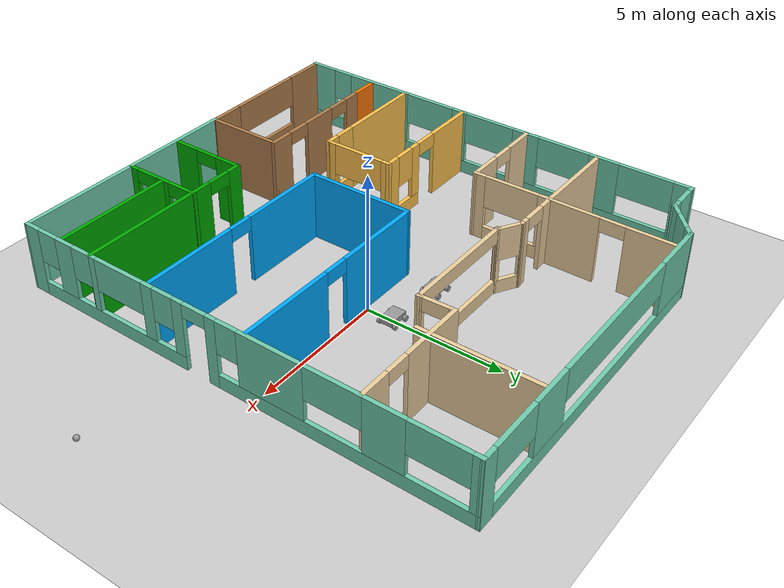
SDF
<sdf version="1.6">
 <world name="default">
  <plugin name="welcome_message" filename="libwelcome_message.so"/>
  <light name="sun" type="directional">
   <pose>0 0 10 0 -0 0</pose>
   <diffuse>0.8 0.8 0.8 1</diffuse>
   <specular>0.2 0.2 0.2 1</specular>
   <attenuation>
    <range>1000</range>
    <constant>0.9</constant>
    <linear>0.01</linear>
    <quadratic>0.001</quadratic>
   </attenuation>
   <direction>-0.5 0.1 -0.9</direction>
  </light>
  <model name="ground_plane">
   <static>1</static>
   <link name="link">
    <collision name="collision">
     <geometry><plane><normal>0 0 1</normal><size>100 100</size></plane></geometry>
     <surface><friction><ode><mu>100</mu><mu2>50</mu2></ode></friction></surface>
    </collision>
    <visual name="visual">
     <cast_shadows>0</cast_shadows>
     <geometry><plane><normal>0 0 1</normal><size>100 100</size></plane></geometry>
     <material>
      <script><uri>file://media/materials/scripts/gazebo.material</uri><name>Gazebo/Grey</name></script>
     </material>
    </visual>
   </link>
  </model>
  <gravity>0 0 -9.8</gravity>
  <magnetic_field>6e-06 2.3e-05 -4.2e-05</magnetic_field>
  <atmosphere type="adiabatic"/>
  <physics name="default_physics" default="0" type="ode">
   <max_step_size>0.001</max_step_size>
   <real_time_factor>1</real_time_factor>
   <real_time_update_rate>1000</real_time_update_rate>
  </physics>
  <scene><ambient>0.4 0.4 0.4 1</ambient><background>0.7 0.7 0.7 1</background><shadows>1</shadows></scene>
  <spherical_coordinates>
   <surface_model>EARTH_WGS84</surface_model>
   <latitude_deg>0</latitude_deg>
   <longitude_deg>0</longitude_deg>
   <elevation>0</elevation>
   <heading_deg>0</heading_deg>
  </spherical_coordinates>
  <model name="rc_bot">
   <link name="link_0">
    <pose>0 0 0.079996 0 -0 0</pose>
    <inertial>
     <mass>1</mass>
     <inertia>
      <ixx>0.166667</ixx>
      <ixy>0</ixy>
      <ixz>0</ixz>
      <iyy>0.166667</iyy>
      <iyz>0</iyz>
      <izz>0.166667</izz>
     </inertia>
    </inertial>
    <visual name="visual">
     <geometry><box><size>0.75 0.5 0.2</size></box></geometry>
     <material>
      <lighting>1</lighting>
      <script><uri>file://media/materials/scripts/gazebo.material</uri><name>Gazebo/Grey</name></script>
      <shader type="pixel"><normal_map>__default__</normal_map></shader>
      <ambient>0.3 0.3 0.3 1</ambient>
      <diffuse>0.7 0.7 0.7 1</diffuse>
      <specular>0.01 0.01 0.01 1</specular>
      <emissive>0 0 0 1</emissive>
     </material>
    </visual>
    <collision name="collision">
     <geometry><box><size>0.75 0.5 0.2</size></box></geometry>
     <surface>
      <friction>
       <ode><mu>1</mu><mu2>1</mu2><fdir1>0 0 0</fdir1><slip1>0</slip1><slip2>0</slip2></ode>
       <torsional>
        <coefficient>1</coefficient>
        <patch_radius>0</patch_radius>
        <surface_radius>0</surface_radius>
        <use_patch_radius>1</use_patch_radius>
        <ode><slip>0</slip></ode>
       </torsional>
      </friction>
      <bounce><restitution_coefficient>0</restitution_coefficient><threshold>1e+06</threshold></bounce>
      <contact>
       <collide_without_contact>0</collide_without_contact>
       <collide_without_contact_bitmask>1</collide_without_contact_bitmask>
       <collide_bitmask>1</collide_bitmask>
       <ode>
        <soft_cfm>0</soft_cfm>
        <soft_erp>0.2</soft_erp>
        <kp>1e+13</kp>
        <kd>1</kd>
        <max_vel>0.01</max_vel>
        <min_depth>0</min_depth>
       </ode>
       <bullet>
        <split_impulse>1</split_impulse>
        <split_impulse_penetration_threshold>-0.01</split_impulse_penetration_threshold>
        <soft_cfm>0</soft_cfm>
        <soft_erp>0.2</soft_erp>
        <kp>1e+13</kp>
        <kd>1</kd>
       </bullet>
      </contact>
     </surface>
    </collision>
   </link>
   <link name="link_1_clone_clone_0">
    <pose>0.275 0.30001 -0.019999 1.5707 -0 0</pose>
    <inertial>
     <mass>1</mass>
     <inertia><ixx>0.145833</ixx><ixy>0</ixy><ixz>0</ixz><iyy>0.145833</iyy><iyz>0</iyz><izz>0.125</izz></inertia>
    </inertial>
    <visual name="visual">
     <geometry><cylinder><radius>0.1</radius><length>0.1</length></cylinder></geometry>
     <material>
      <lighting>1</lighting>
      <script><uri>file://media/materials/scripts/gazebo.material</uri><name>Gazebo/Grey</name></script>
      <shader type="pixel"><normal_map>__default__</normal_map></shader>
      <ambient>0.3 0.3 0.3 1</ambient>
      <diffuse>0.7 0.7 0.7 1</diffuse>
      <specular>0.01 0.01 0.01 1</specular>
      <emissive>0 0 0 1</emissive>
     </material>
    </visual>
    <collision name="collision">
     <geometry><cylinder><radius>0.1</radius><length>0.1</length></cylinder></geometry>
     <surface>
      <friction>
       <ode><mu>1</mu><mu2>1</mu2><fdir1>0 0 0</fdir1><slip1>0</slip1><slip2>0</slip2></ode>
       <torsional>
        <coefficient>1</coefficient>
        <patch_radius>0</patch_radius>
        <surface_radius>0</surface_radius>
        <use_patch_radius>1</use_patch_radius>
        <ode><slip>0</slip></ode>
       </torsional>
      </friction>
      <bounce><restitution_coefficient>0</restitution_coefficient><threshold>1e+06</threshold></bounce>
      <contact>
       <collide_without_contact>0</collide_without_contact>
       <collide_without_contact_bitmask>1</collide_without_contact_bitmask>
       <collide_bitmask>1</collide_bitmask>
       <ode>
        <soft_cfm>0</soft_cfm>
        <soft_erp>0.2</soft_erp>
        <kp>1e+13</kp>
        <kd>1</kd>
        <max_vel>0.01</max_vel>
        <min_depth>0</min_depth>
       </ode>
       <bullet>
        <split_impulse>1</split_impulse>
        <split_impulse_penetration_threshold>-0.01</split_impulse_penetration_threshold>
        <soft_cfm>0</soft_cfm>
        <soft_erp>0.2</soft_erp>
        <kp>1e+13</kp>
        <kd>1</kd>
       </bullet>
      </contact>
     </surface>
    </collision>
   </link>
   <link name="link_1_clone_clone_0_clone">
    <pose>-0.275 0.30001 -0.019999 1.5707 -0 0</pose>
    <inertial>
     <mass>1</mass>
     <inertia><ixx>0.145833</ixx><ixy>0</ixy><ixz>0</ixz><iyy>0.145833</iyy><iyz>0</iyz><izz>0.125</izz></inertia>
    </inertial>
    <visual name="visual">
     <geometry><cylinder><radius>0.1</radius><length>0.1</length></cylinder></geometry>
     <material>
      <lighting>1</lighting>
      <script><uri>file://media/materials/scripts/gazebo.material</uri><name>Gazebo/Grey</name></script>
      <shader type="pixel"><normal_map>__default__</normal_map></shader>
      <ambient>0.3 0.3 0.3 1</ambient>
      <diffuse>0.7 0.7 0.7 1</diffuse>
      <specular>0.01 0.01 0.01 1</specular>
      <emissive>0 0 0 1</emissive>
     </material>
    </visual>
    <collision name="collision">
     <geometry><cylinder><radius>0.1</radius><length>0.1</length></cylinder></geometry>
     <surface>
      <friction>
       <ode><mu>1</mu><mu2>1</mu2><fdir1>0 0 0</fdir1><slip1>0</slip1><slip2>0</slip2></ode>
       <torsional>
        <coefficient>1</coefficient>
        <patch_radius>0</patch_radius>
        <surface_radius>0</surface_radius>
        <use_patch_radius>1</use_patch_radius>
        <ode><slip>0</slip></ode>
       </torsional>
      </friction>
      <bounce><restitution_coefficient>0</restitution_coefficient><threshold>1e+06</threshold></bounce>
      <contact>
       <collide_without_contact>0</collide_without_contact>
       <collide_without_contact_bitmask>1</collide_without_contact_bitmask>
       <collide_bitmask>1</collide_bitmask>
       <ode>
        <soft_cfm>0</soft_cfm>
        <soft_erp>0.2</soft_erp>
        <kp>1e+13</kp>
        <kd>1</kd>
        <max_vel>0.01</max_vel>
        <min_depth>0</min_depth>
       </ode>
       <bullet>
        <split_impulse>1</split_impulse>
        <split_impulse_penetration_threshold>-0.01</split_impulse_penetration_threshold>
        <soft_cfm>0</soft_cfm>
        <soft_erp>0.2</soft_erp>
        <kp>1e+13</kp>
        <kd>1</kd>
       </bullet>
      </contact>
     </surface>
    </collision>
   </link>
   <link name="link_1_clone_clone_0_clone_0">
    <pose>0.275 -0.30001 -0.019999 1.5707 -0 0</pose>
    <inertial>
     <mass>1</mass>
     <inertia><ixx>0.145833</ixx><ixy>0</ixy><ixz>0</ixz><iyy>0.145833</iyy><iyz>0</iyz><izz>0.125</izz></inertia>
    </inertial>
    <visual name="visual">
     <geometry><cylinder><radius>0.1</radius><length>0.1</length></cylinder></geometry>
     <material>
      <lighting>1</lighting>
      <script><uri>file://media/materials/scripts/gazebo.material</uri><name>Gazebo/Grey</name></script>
      <shader type="pixel"><normal_map>__default__</normal_map></shader>
      <ambient>0.3 0.3 0.3 1</ambient>
      <diffuse>0.7 0.7 0.7 1</diffuse>
      <specular>0.01 0.01 0.01 1</specular>
      <emissive>0 0 0 1</emissive>
     </material>
    </visual>
    <collision name="collision">
     <geometry><cylinder><radius>0.1</radius><length>0.1</length></cylinder></geometry>
     <surface>
      <friction>
       <ode><mu>1</mu><mu2>1</mu2><fdir1>0 0 0</fdir1><slip1>0</slip1><slip2>0</slip2></ode>
       <torsional>
        <coefficient>1</coefficient>
        <patch_radius>0</patch_radius>
        <surface_radius>0</surface_radius>
        <use_patch_radius>1</use_patch_radius>
        <ode><slip>0</slip></ode>
       </torsional>
      </friction>
      <bounce><restitution_coefficient>0</restitution_coefficient><threshold>1e+06</threshold></bounce>
      <contact>
       <collide_without_contact>0</collide_without_contact>
       <collide_without_contact_bitmask>1</collide_without_contact_bitmask>
       <collide_bitmask>1</collide_bitmask>
       <ode>
        <soft_cfm>0</soft_cfm>
        <soft_erp>0.2</soft_erp>
        <kp>1e+13</kp>
        <kd>1</kd>
        <max_vel>0.01</max_vel>
        <min_depth>0</min_depth>
       </ode>
       <bullet>
        <split_impulse>1</split_impulse>
        <split_impulse_penetration_threshold>-0.01</split_impulse_penetration_threshold>
        <soft_cfm>0</soft_cfm>
        <soft_erp>0.2</soft_erp>
        <kp>1e+13</kp>
        <kd>1</kd>
       </bullet>
      </contact>
     </surface>
    </collision>
   </link>
   <link name="link_1_clone_clone_0_clone_1">
    <pose>-0.275 -0.30001 -0.019999 1.5707 -0 0</pose>
    <inertial>
     <mass>1</mass>
     <inertia><ixx>0.145833</ixx><ixy>0</ixy><ixz>0</ixz><iyy>0.145833</iyy><iyz>0</iyz><izz>0.125</izz></inertia>
    </inertial>
    <visual name="visual">
     <geometry><cylinder><radius>0.1</radius><length>0.1</length></cylinder></geometry>
     <material>
      <lighting>1</lighting>
      <script><uri>file://media/materials/scripts/gazebo.material</uri><name>Gazebo/Grey</name></script>
      <shader type="pixel"><normal_map>__default__</normal_map></shader>
      <ambient>0.3 0.3 0.3 1</ambient>
      <diffuse>0.7 0.7 0.7 1</diffuse>
      <specular>0.01 0.01 0.01 1</specular>
      <emissive>0 0 0 1</emissive>
     </material>
    </visual>
    <collision name="collision">
     <geometry><cylinder><radius>0.1</radius><length>0.1</length></cylinder></geometry>
     <surface>
      <friction>
       <ode><mu>1</mu><mu2>1</mu2><fdir1>0 0 0</fdir1><slip1>0</slip1><slip2>0</slip2></ode>
       <torsional>
        <coefficient>1</coefficient>
        <patch_radius>0</patch_radius>
        <surface_radius>0</surface_radius>
        <use_patch_radius>1</use_patch_radius>
        <ode><slip>0</slip></ode>
       </torsional>
      </friction>
      <bounce><restitution_coefficient>0</restitution_coefficient><threshold>1e+06</threshold></bounce>
      <contact>
       <collide_without_contact>0</collide_without_contact>
       <collide_without_contact_bitmask>1</collide_without_contact_bitmask>
       <collide_bitmask>1</collide_bitmask>
       <ode>
        <soft_cfm>0</soft_cfm>
        <soft_erp>0.2</soft_erp>
        <kp>1e+13</kp>
        <kd>1</kd>
        <max_vel>0.01</max_vel>
        <min_depth>0</min_depth>
       </ode>
       <bullet>
        <split_impulse>1</split_impulse>
        <split_impulse_penetration_threshold>-0.01</split_impulse_penetration_threshold>
        <soft_cfm>0</soft_cfm>
        <soft_erp>0.2</soft_erp>
        <kp>1e+13</kp>
        <kd>1</kd>
       </bullet>
      </contact>
     </surface>
    </collision>
   </link>
   <joint name="link_0_JOINT_0" type="revolute">
    <parent>link_0</parent>
    <child>link_1_clone_clone_0</child>
    <axis>
     <xyz>0 0 1</xyz>
     <use_parent_model_frame>0</use_parent_model_frame>
     <limit>
      <lower>-1.79769e+308</lower>
      <upper>1.79769e+308</upper>
      <effort>-1</effort>
      <velocity>-1</velocity>
     </limit>
     <dynamics>
      <spring_reference>0</spring_reference>
      <spring_stiffness>0</spring_stiffness>
      <damping>0</damping>
      <friction>0</friction>
     </dynamics>
    </axis>
    <physics>
     <ode><limit><cfm>0</cfm><erp>0.2</erp></limit><suspension><cfm>0</cfm><erp>0.2</erp></suspension></ode>
    </physics>
   </joint>
   <joint name="link_0_JOINT_3" type="revolute">
    <parent>link_0</parent>
    <child>link_1_clone_clone_0_clone</child>
    <axis>
     <xyz>0 0 1</xyz>
     <use_parent_model_frame>0</use_parent_model_frame>
     <limit>
      <lower>-1.79769e+308</lower>
      <upper>1.79769e+308</upper>
      <effort>-1</effort>
      <velocity>-1</velocity>
     </limit>
     <dynamics>
      <spring_reference>0</spring_reference>
      <spring_stiffness>0</spring_stiffness>
      <damping>0</damping>
     </dynamics>
    </axis>
    <physics>
     <ode><limit><cfm>0</cfm><erp>0.2</erp></limit><suspension><cfm>0</cfm><erp>0.2</erp></suspension></ode>
    </physics>
   </joint>
   <joint name="link_0_JOINT_4" type="revolute">
    <parent>link_0</parent>
    <child>link_1_clone_clone_0_clone_0</child>
    <axis>
     <xyz>0 0 1</xyz>
     <use_parent_model_frame>0</use_parent_model_frame>
     <limit>
      <lower>-1.79769e+308</lower>
      <upper>1.79769e+308</upper>
      <effort>-1</effort>
      <velocity>-1</velocity>
     </limit>
     <dynamics>
      <spring_reference>0</spring_reference>
      <spring_stiffness>0</spring_stiffness>
      <damping>0</damping>
     </dynamics>
    </axis>
    <physics>
     <ode><limit><cfm>0</cfm><erp>0.2</erp></limit><suspension><cfm>0</cfm><erp>0.2</erp></suspension></ode>
    </physics>
   </joint>
   <joint name="link_0_JOINT_5" type="revolute">
    <parent>link_0</parent>
    <child>link_1_clone_clone_0_clone_1</child>
    <axis>
     <xyz>0 0 1</xyz>
     <use_parent_model_frame>0</use_parent_model_frame>
     <limit>
      <lower>-1.79769e+308</lower>
      <upper>1.79769e+308</upper>
      <effort>-1</effort>
      <velocity>-1</velocity>
     </limit>
     <dynamics>
      <spring_reference>0</spring_reference>
      <spring_stiffness>0</spring_stiffness>
      <damping>0</damping>
     </dynamics>
    </axis>
    <physics>
     <ode><limit><cfm>0</cfm><erp>0.2</erp></limit><suspension><cfm>0</cfm><erp>0.2</erp></suspension></ode>
    </physics>
   </joint>
   <static>0</static>
   <pose>0.000248 0.974739 0.12 0 1.4e-05 -0.000899</pose>
  </model>
  <model name="Building-1">
   <pose>-1.79482 -0.84337 0 0 -0 0</pose>
   <link name="Wall_101">
    <collision name="Wall_101_Collision">
     <geometry><box><size>1 0.15 2.5</size></box></geometry>
     <pose>0 0 1.25 0 -0 0</pose>
    </collision>
    <visual name="Wall_101_Visual">
     <pose>0 0 1.25 0 -0 0</pose>
     <geometry><box><size>1 0.15 2.5</size></box></geometry>
     <material>
      <script><uri>file://media/materials/scripts/gazebo.material</uri><name>Gazebo/Grey</name></script>
      <ambient>0.996078 0.47451 0.0196078 1</ambient>
     </material>
     <meta><layer>0</layer></meta>
    </visual>
    <pose>-6.64557 -5.66391 0 0 -0 0</pose>
   </link>
   <link name="Wall_55">
    <pose>-3.79556 -5.66391 0 0 -0 0</pose>
    <visual name="Wall_55_Visual_0">
     <pose>-2.08336 0 1.25 0 -0 0</pose>
     <geometry><box><size>0.833273 0.15 2.5</size></box></geometry>
     <material>
      <script><uri>file://media/materials/scripts/gazebo.material</uri><name>Gazebo/Wood</name></script>
      <ambient>0.996078 0.47451 0.0196078 1</ambient>
     </material>
     <meta><layer>0</layer></meta>
    </visual>
    <collision name="Wall_55_Collision_0">
     <geometry><box><size>0.833273 0.15 2.5</size></box></geometry>
     <pose>-2.08336 0 1.25 0 -0 0</pose>
    </collision>
    <visual name="Wall_55_Visual_1">
     <pose>-0.059292 0 1.25 0 -0 0</pose>
     <geometry><box><size>1.41487 0.15 2.5</size></box></geometry>
     <material>
      <script><uri>file://media/materials/scripts/gazebo.material</uri><name>Gazebo/Wood</name></script>
      <ambient>0.996078 0.47451 0.0196078 1</ambient>
     </material>
     <meta><layer>0</layer></meta>
    </visual>
    <collision name="Wall_55_Collision_1">
     <geometry><box><size>1.41487 0.15 2.5</size></box></geometry>
     <pose>-0.059292 0 1.25 0 -0 0</pose>
    </collision>
    <visual name="Wall_55_Visual_2">
     <pose>2.02407 0 1.25 0 -0 0</pose>
     <geometry><box><size>0.951857 0.15 2.5</size></box></geometry>
     <material>
      <script><uri>file://media/materials/scripts/gazebo.material</uri><name>Gazebo/Wood</name></script>
      <ambient>0.996078 0.47451 0.0196078 1</ambient>
     </material>
     <meta><layer>0</layer></meta>
    </visual>
    <collision name="Wall_55_Collision_2">
     <geometry><box><size>0.951857 0.15 2.5</size></box></geometry>
     <pose>2.02407 0 1.25 0 -0 0</pose>
    </collision>
    <visual name="Wall_55_Visual_3">
     <pose>-1.21673 0 2.25 0 -0 0</pose>
     <geometry><box><size>0.9 0.15 0.5</size></box></geometry>
     <material>
      <script><uri>file://media/materials/scripts/gazebo.material</uri><name>Gazebo/Wood</name></script>
      <ambient>0.996078 0.47451 0.0196078 1</ambient>
     </material>
     <meta><layer>0</layer></meta>
    </visual>
    <collision name="Wall_55_Collision_3">
     <geometry><box><size>0.9 0.15 0.5</size></box></geometry>
     <pose>-1.21673 0 2.25 0 -0 0</pose>
    </collision>
    <visual name="Wall_55_Visual_4">
     <pose>1.09814 0 2.25 0 -0 0</pose>
     <geometry><box><size>0.9 0.15 0.5</size></box></geometry>
     <material>
      <script><uri>file://media/materials/scripts/gazebo.material</uri><name>Gazebo/Wood</name></script>
      <ambient>0.996078 0.47451 0.0196078 1</ambient>
     </material>
     <meta><layer>0</layer></meta>
    </visual>
    <collision name="Wall_55_Collision_4">
     <geometry><box><size>0.9 0.15 0.5</size></box></geometry>
     <pose>1.09814 0 2.25 0 -0 0</pose>
    </collision>
   </link>
   <link name="Wall_56">
    <collision name="Wall_56_Collision">
     <geometry><box><size>3 0.15 2.5</size></box></geometry>
     <pose>0 0 1.25 0 -0 0</pose>
    </collision>
    <visual name="Wall_56_Visual">
     <pose>0 0 1.25 0 -0 0</pose>
     <geometry><box><size>3 0.15 2.5</size></box></geometry>
     <material>
      <script><uri>file://media/materials/scripts/gazebo.material</uri><name>Gazebo/Wood</name></script>
      <ambient>0.996078 0.47451 0.0196078 1</ambient>
     </material>
     <meta><layer>0</layer></meta>
    </visual>
    <pose>-1.37057 -7.08891 0 0 0 -1.5708</pose>
   </link>
   <link name="Wall_57">
    <collision name="Wall_57_Collision">
     <geometry><box><size>8.75 0.15 2.5</size></box></geometry>
     <pose>0 0 1.25 0 -0 0</pose>
    </collision>
    <visual name="Wall_57_Visual">
     <pose>0 0 1.25 0 -0 0</pose>
     <geometry><box><size>8.75 0.15 2.5</size></box></geometry>
     <material>
      <script><uri>file://media/materials/scripts/gazebo.material</uri><name>Gazebo/Grey</name></script>
      <ambient>0.435294 0.796078 0.67451 1</ambient>
     </material>
     <meta><layer>0</layer></meta>
    </visual>
    <pose>2.92943 -8.51391 0 0 -0 0</pose>
   </link>
   <link name="Wall_58">
    <pose>7.27698 -0.015167 0 0 -0 1.5652</pose>
    <visual name="Wall_58_Visual_0">
     <pose>-8.25726 0 1.25 0 -0 0</pose>
     <geometry><box><size>0.633232 0.15 2.5</size></box></geometry>
     <material>
      <script><uri>file://media/materials/scripts/gazebo.material</uri><name>Gazebo/Grey</name></script>
      <ambient>0.435294 0.796078 0.67451 1</ambient>
     </material>
     <meta><layer>0</layer></meta>
    </visual>
    <collision name="Wall_58_Collision_0">
     <geometry><box><size>0.633232 0.15 2.5</size></box></geometry>
     <pose>-8.25726 0 1.25 0 -0 0</pose>
    </collision>
    <visual name="Wall_58_Visual_1">
     <pose>-0.583033 0 1.25 0 -0 0</pose>
     <geometry><box><size>0.396965 0.15 2.5</size></box></geometry>
     <material>
      <script><uri>file://media/materials/scripts/gazebo.material</uri><name>Gazebo/Grey</name></script>
      <ambient>0.435294 0.796078 0.67451 1</ambient>
     </material>
     <meta><layer>0</layer></meta>
    </visual>
    <collision name="Wall_58_Collision_1">
     <geometry><box><size>0.396965 0.15 2.5</size></box></geometry>
     <pose>-0.583033 0 1.25 0 -0 0</pose>
    </collision>
    <visual name="Wall_58_Visual_2">
     <pose>-4.81108 0 0.25 0 -0 0</pose>
     <geometry><box><size>6.25913 0.15 0.5</size></box></geometry>
     <material>
      <script><uri>file://media/materials/scripts/gazebo.material</uri><name>Gazebo/Grey</name></script>
      <ambient>0.435294 0.796078 0.67451 1</ambient>
     </material>
     <meta><layer>0</layer></meta>
    </visual>
    <collision name="Wall_58_Collision_2">
     <geometry><box><size>6.25913 0.15 0.5</size></box></geometry>
     <pose>-4.81108 0 0.25 0 -0 0</pose>
    </collision>
    <visual name="Wall_58_Visual_3">
     <pose>4.09466 0 0.25 0 -0 0</pose>
     <geometry><box><size>8.95843 0.15 0.5</size></box></geometry>
     <material>
      <script><uri>file://media/materials/scripts/gazebo.material</uri><name>Gazebo/Grey</name></script>
      <ambient>0.435294 0.796078 0.67451 1</ambient>
     </material>
     <meta><layer>0</layer></meta>
    </visual>
    <collision name="Wall_58_Collision_3">
     <geometry><box><size>8.95843 0.15 0.5</size></box></geometry>
     <pose>4.09466 0 0.25 0 -0 0</pose>
    </collision>
    <visual name="Wall_58_Visual_4">
     <pose>-6.76763 0 1.5 0 -0 0</pose>
     <geometry><box><size>0.746033 0.15 2</size></box></geometry>
     <material>
      <script><uri>file://media/materials/scripts/gazebo.material</uri><name>Gazebo/Grey</name></script>
      <ambient>0.435294 0.796078 0.67451 1</ambient>
     </material>
     <meta><layer>0</layer></meta>
    </visual>
    <collision name="Wall_58_Collision_4">
     <geometry><box><size>0.746033 0.15 2</size></box></geometry>
     <pose>-6.76763 0 1.5 0 -0 0</pose>
    </collision>
    <visual name="Wall_58_Visual_5">
     <pose>-5.47131 0 1.5 0 -0 0</pose>
     <geometry><box><size>0.246602 0.15 2</size></box></geometry>
     <material>
      <script><uri>file://media/materials/scripts/gazebo.material</uri><name>Gazebo/Grey</name></script>
      <ambient>0.435294 0.796078 0.67451 1</ambient>
     </material>
     <meta><layer>0</layer></meta>
    </visual>
    <collision name="Wall_58_Collision_5">
     <geometry><box><size>0.246602 0.15 2</size></box></geometry>
     <pose>-5.47131 0 1.5 0 -0 0</pose>
    </collision>
    <visual name="Wall_58_Visual_6">
     <pose>-3.12103 0 1.5 0 -0 0</pose>
     <geometry><box><size>0.453955 0.15 2</size></box></geometry>
     <material>
      <script><uri>file://media/materials/scripts/gazebo.material</uri><name>Gazebo/Grey</name></script>
      <ambient>0.435294 0.796078 0.67451 1</ambient>
     </material>
     <meta><layer>0</layer></meta>
    </visual>
    <collision name="Wall_58_Collision_6">
     <geometry><box><size>0.453955 0.15 2</size></box></geometry>
     <pose>-3.12103 0 1.5 0 -0 0</pose>
    </collision>
    <visual name="Wall_58_Visual_7">
     <pose>-1.88778 0 1.5 0 -0 0</pose>
     <geometry><box><size>0.412539 0.15 2</size></box></geometry>
     <material>
      <script><uri>file://media/materials/scripts/gazebo.material</uri><name>Gazebo/Grey</name></script>
      <ambient>0.435294 0.796078 0.67451 1</ambient>
     </material>
     <meta><layer>0</layer></meta>
    </visual>
    <collision name="Wall_58_Collision_7">
     <geometry><box><size>0.412539 0.15 2</size></box></geometry>
     <pose>-1.88778 0 1.5 0 -0 0</pose>
    </collision>
    <visual name="Wall_58_Visual_8">
     <pose>-1.88778 0 1.5 0 -0 0</pose>
     <geometry><box><size>0.412539 0.15 2</size></box></geometry>
     <material>
      <script><uri>file://media/materials/scripts/gazebo.material</uri><name>Gazebo/Grey</name></script>
      <ambient>0.435294 0.796078 0.67451 1</ambient>
     </material>
     <meta><layer>0</layer></meta>
    </visual>
    <collision name="Wall_58_Collision_8">
     <geometry><box><size>0.412539 0.15 2</size></box></geometry>
     <pose>-1.88778 0 1.5 0 -0 0</pose>
    </collision>
    <visual name="Wall_58_Visual_9">
     <pose>1.61766 0 1.5 0 -0 0</pose>
     <geometry><box><size>2.40442 0.15 2</size></box></geometry>
     <material>
      <script><uri>file://media/materials/scripts/gazebo.material</uri><name>Gazebo/Grey</name></script>
      <ambient>0.435294 0.796078 0.67451 1</ambient>
     </material>
     <meta><layer>0</layer></meta>
    </visual>
    <collision name="Wall_58_Collision_9">
     <geometry><box><size>2.40442 0.15 2</size></box></geometry>
     <pose>1.61766 0 1.5 0 -0 0</pose>
    </collision>
    <visual name="Wall_58_Visual_10">
     <pose>5.52613 0 1.5 0 -0 0</pose>
     <geometry><box><size>1.41252 0.15 2</size></box></geometry>
     <material>
      <script><uri>file://media/materials/scripts/gazebo.material</uri><name>Gazebo/Grey</name></script>
      <ambient>0.435294 0.796078 0.67451 1</ambient>
     </material>
     <meta><layer>0</layer></meta>
    </visual>
    <collision name="Wall_58_Collision_10">
     <geometry><box><size>1.41252 0.15 2</size></box></geometry>
     <pose>5.52613 0 1.5 0 -0 0</pose>
    </collision>
    <visual name="Wall_58_Visual_11">
     <pose>8.40314 0 1.5 0 -0 0</pose>
     <geometry><box><size>0.341482 0.15 2</size></box></geometry>
     <material>
      <script><uri>file://media/materials/scripts/gazebo.material</uri><name>Gazebo/Grey</name></script>
      <ambient>0.435294 0.796078 0.67451 1</ambient>
     </material>
     <meta><layer>0</layer></meta>
    </visual>
    <collision name="Wall_58_Collision_11">
     <geometry><box><size>0.341482 0.15 2</size></box></geometry>
     <pose>8.40314 0 1.5 0 -0 0</pose>
    </collision>
    <visual name="Wall_58_Visual_12">
     <pose>-7.54064 0 1.9 0 -0 0</pose>
     <geometry><box><size>0.8 0.15 1.2</size></box></geometry>
     <material>
      <script><uri>file://media/materials/scripts/gazebo.material</uri><name>Gazebo/Grey</name></script>
      <ambient>0.435294 0.796078 0.67451 1</ambient>
     </material>
     <meta><layer>0</layer></meta>
    </visual>
    <collision name="Wall_58_Collision_12">
     <geometry><box><size>0.8 0.15 1.2</size></box></geometry>
     <pose>-7.54064 0 1.9 0 -0 0</pose>
    </collision>
    <visual name="Wall_58_Visual_13">
     <pose>0.01545 0 1.9 0 -0 0</pose>
     <geometry><box><size>0.8 0.15 1.2</size></box></geometry>
     <material>
      <script><uri>file://media/materials/scripts/gazebo.material</uri><name>Gazebo/Grey</name></script>
      <ambient>0.435294 0.796078 0.67451 1</ambient>
     </material>
     <meta><layer>0</layer></meta>
    </visual>
    <collision name="Wall_58_Collision_13">
     <geometry><box><size>0.8 0.15 1.2</size></box></geometry>
     <pose>0.01545 0 1.9 0 -0 0</pose>
    </collision>
    <visual name="Wall_58_Visual_14">
     <pose>-5.99461 0 1.9 0 -0 0</pose>
     <geometry><box><size>0.8 0.15 1.2</size></box></geometry>
     <material>
      <script><uri>file://media/materials/scripts/gazebo.material</uri><name>Gazebo/Grey</name></script>
      <ambient>0.435294 0.796078 0.67451 1</ambient>
     </material>
     <meta><layer>0</layer></meta>
    </visual>
    <collision name="Wall_58_Collision_14">
     <geometry><box><size>0.8 0.15 1.2</size></box></geometry>
     <pose>-5.99461 0 1.9 0 -0 0</pose>
    </collision>
    <visual name="Wall_58_Visual_15">
     <pose>-4.34801 0 1.9 0 -0 0</pose>
     <geometry><box><size>2 0.15 1.2</size></box></geometry>
     <material>
      <script><uri>file://media/materials/scripts/gazebo.material</uri><name>Gazebo/Grey</name></script>
      <ambient>0.435294 0.796078 0.67451 1</ambient>
     </material>
     <meta><layer>0</layer></meta>
    </visual>
    <collision name="Wall_58_Collision_15">
     <geometry><box><size>2 0.15 1.2</size></box></geometry>
     <pose>-4.34801 0 1.9 0 -0 0</pose>
    </collision>
    <visual name="Wall_58_Visual_16">
     <pose>-2.49405 0 1.9 0 -0 0</pose>
     <geometry><box><size>0.8 0.15 1.2</size></box></geometry>
     <material>
      <script><uri>file://media/materials/scripts/gazebo.material</uri><name>Gazebo/Grey</name></script>
      <ambient>0.435294 0.796078 0.67451 1</ambient>
     </material>
     <meta><layer>0</layer></meta>
    </visual>
    <collision name="Wall_58_Collision_16">
     <geometry><box><size>0.8 0.15 1.2</size></box></geometry>
     <pose>-2.49405 0 1.9 0 -0 0</pose>
    </collision>
    <visual name="Wall_58_Visual_17">
     <pose>3.81987 0 1.9 0 -0 0</pose>
     <geometry><box><size>2 0.15 1.2</size></box></geometry>
     <material>
      <script><uri>file://media/materials/scripts/gazebo.material</uri><name>Gazebo/Grey</name></script>
      <ambient>0.435294 0.796078 0.67451 1</ambient>
     </material>
     <meta><layer>0</layer></meta>
    </visual>
    <collision name="Wall_58_Collision_17">
     <geometry><box><size>2 0.15 1.2</size></box></geometry>
     <pose>3.81987 0 1.9 0 -0 0</pose>
    </collision>
    <visual name="Wall_58_Visual_18">
     <pose>7.23239 0 1.9 0 -0 0</pose>
     <geometry><box><size>2 0.15 1.2</size></box></geometry>
     <material>
      <script><uri>file://media/materials/scripts/gazebo.material</uri><name>Gazebo/Grey</name></script>
      <ambient>0.435294 0.796078 0.67451 1</ambient>
     </material>
     <meta><layer>0</layer></meta>
    </visual>
    <collision name="Wall_58_Collision_18">
     <geometry><box><size>2 0.15 1.2</size></box></geometry>
     <pose>7.23239 0 1.9 0 -0 0</pose>
    </collision>
    <visual name="Wall_58_Visual_19">
     <pose>-1.23151 0 2.25 0 -0 0</pose>
     <geometry><box><size>0.9 0.15 0.5</size></box></geometry>
     <material>
      <script><uri>file://media/materials/scripts/gazebo.material</uri><name>Gazebo/Grey</name></script>
      <ambient>0.435294 0.796078 0.67451 1</ambient>
     </material>
     <meta><layer>0</layer></meta>
    </visual>
    <collision name="Wall_58_Collision_19">
     <geometry><box><size>0.9 0.15 0.5</size></box></geometry>
     <pose>-1.23151 0 2.25 0 -0 0</pose>
    </collision>
    <visual name="Wall_58_Visual_20">
     <pose>-1.23151 0 2.25 0 -0 0</pose>
     <geometry><box><size>0.9 0.15 0.5</size></box></geometry>
     <material>
      <script><uri>file://media/materials/scripts/gazebo.material</uri><name>Gazebo/Grey</name></script>
      <ambient>0.435294 0.796078 0.67451 1</ambient>
     </material>
     <meta><layer>0</layer></meta>
    </visual>
    <collision name="Wall_58_Collision_20">
     <geometry><box><size>0.9 0.15 0.5</size></box></geometry>
     <pose>-1.23151 0 2.25 0 -0 0</pose>
    </collision>
   </link>
   <link name="Wall_59">
    <pose>1.27452 8.50244 0 0 -0 3.14159</pose>
    <visual name="Wall_59_Visual_0">
     <pose>-5.83178 0 1.25 0 -0 0</pose>
     <geometry><box><size>0.586429 0.15 2.5</size></box></geometry>
     <material>
      <script><uri>file://media/materials/scripts/gazebo.material</uri><name>Gazebo/Grey</name></script>
      <ambient>0.435294 0.796078 0.67451 1</ambient>
     </material>
     <meta><layer>0</layer></meta>
    </visual>
    <collision name="Wall_59_Collision_0">
     <geometry><box><size>0.586429 0.15 2.5</size></box></geometry>
     <pose>-5.83178 0 1.25 0 -0 0</pose>
    </collision>
    <visual name="Wall_59_Visual_1">
     <pose>0.293215 0 0.25 0 -0 0</pose>
     <geometry><box><size>11.6636 0.15 0.5</size></box></geometry>
     <material>
      <script><uri>file://media/materials/scripts/gazebo.material</uri><name>Gazebo/Grey</name></script>
      <ambient>0.435294 0.796078 0.67451 1</ambient>
     </material>
     <meta><layer>0</layer></meta>
    </visual>
    <collision name="Wall_59_Collision_1">
     <geometry><box><size>11.6636 0.15 0.5</size></box></geometry>
     <pose>0.293215 0 0.25 0 -0 0</pose>
    </collision>
    <visual name="Wall_59_Visual_2">
     <pose>-2.72513 0 1.5 0 -0 0</pose>
     <geometry><box><size>1.62688 0.15 2</size></box></geometry>
     <material>
      <script><uri>file://media/materials/scripts/gazebo.material</uri><name>Gazebo/Grey</name></script>
      <ambient>0.435294 0.796078 0.67451 1</ambient>
     </material>
     <meta><layer>0</layer></meta>
    </visual>
    <collision name="Wall_59_Collision_2">
     <geometry><box><size>1.62688 0.15 2</size></box></geometry>
     <pose>-2.72513 0 1.5 0 -0 0</pose>
    </collision>
    <visual name="Wall_59_Visual_3">
     <pose>5.10665 0 1.5 0 -0 0</pose>
     <geometry><box><size>2.03669 0.15 2</size></box></geometry>
     <material>
      <script><uri>file://media/materials/scripts/gazebo.material</uri><name>Gazebo/Grey</name></script>
      <ambient>0.435294 0.796078 0.67451 1</ambient>
     </material>
     <meta><layer>0</layer></meta>
    </visual>
    <collision name="Wall_59_Collision_3">
     <geometry><box><size>2.03669 0.15 2</size></box></geometry>
     <pose>5.10665 0 1.5 0 -0 0</pose>
    </collision>
    <visual name="Wall_59_Visual_4">
     <pose>-4.53857 0 1.9 0 -0 0</pose>
     <geometry><box><size>2 0.15 1.2</size></box></geometry>
     <material>
      <script><uri>file://media/materials/scripts/gazebo.material</uri><name>Gazebo/Grey</name></script>
      <ambient>0.435294 0.796078 0.67451 1</ambient>
     </material>
     <meta><layer>0</layer></meta>
    </visual>
    <collision name="Wall_59_Collision_4">
     <geometry><box><size>2 0.15 1.2</size></box></geometry>
     <pose>-4.53857 0 1.9 0 -0 0</pose>
    </collision>
    <visual name="Wall_59_Visual_5">
     <pose>1.08831 0 1.9 0 -0 0</pose>
     <geometry><box><size>6 0.15 1.2</size></box></geometry>
     <material>
      <script><uri>file://media/materials/scripts/gazebo.material</uri><name>Gazebo/Grey</name></script>
      <ambient>0.435294 0.796078 0.67451 1</ambient>
     </material>
     <meta><layer>0</layer></meta>
    </visual>
    <collision name="Wall_59_Collision_5">
     <geometry><box><size>6 0.15 1.2</size></box></geometry>
     <pose>1.08831 0 1.9 0 -0 0</pose>
    </collision>
   </link>
   <link name="Wall_60">
    <pose>-5.41275 7.93742 0 0 0 -2.43304</pose>
    <visual name="Wall_60_Visual_0">
     <pose>-0.703208 0 1.25 0 -0 0</pose>
     <geometry><box><size>0.422171 0.15 2.5</size></box></geometry>
     <material>
      <script><uri>file://media/materials/scripts/gazebo.material</uri><name>Gazebo/Grey</name></script>
      <ambient>0.435294 0.796078 0.67451 1</ambient>
     </material>
     <meta><layer>0</layer></meta>
    </visual>
    <collision name="Wall_60_Collision_0">
     <geometry><box><size>0.422171 0.15 2.5</size></box></geometry>
     <pose>-0.703208 0 1.25 0 -0 0</pose>
    </collision>
    <visual name="Wall_60_Visual_1">
     <pose>0.211086 0 0.25 0 -0 0</pose>
     <geometry><box><size>1.40642 0.15 0.5</size></box></geometry>
     <material>
      <script><uri>file://media/materials/scripts/gazebo.material</uri><name>Gazebo/Grey</name></script>
      <ambient>0.435294 0.796078 0.67451 1</ambient>
     </material>
     <meta><layer>0</layer></meta>
    </visual>
    <collision name="Wall_60_Collision_1">
     <geometry><box><size>1.40642 0.15 0.5</size></box></geometry>
     <pose>0.211086 0 0.25 0 -0 0</pose>
    </collision>
    <visual name="Wall_60_Visual_2">
     <pose>0.611086 0 1.5 0 -0 0</pose>
     <geometry><box><size>0.606416 0.15 2</size></box></geometry>
     <material>
      <script><uri>file://media/materials/scripts/gazebo.material</uri><name>Gazebo/Grey</name></script>
      <ambient>0.435294 0.796078 0.67451 1</ambient>
     </material>
     <meta><layer>0</layer></meta>
    </visual>
    <collision name="Wall_60_Collision_2">
     <geometry><box><size>0.606416 0.15 2</size></box></geometry>
     <pose>0.611086 0 1.5 0 -0 0</pose>
    </collision>
    <visual name="Wall_60_Visual_3">
     <pose>-0.092122 0 1.9 0 -0 0</pose>
     <geometry><box><size>0.8 0.15 1.2</size></box></geometry>
     <material>
      <script><uri>file://media/materials/scripts/gazebo.material</uri><name>Gazebo/Grey</name></script>
      <ambient>0.435294 0.796078 0.67451 1</ambient>
     </material>
     <meta><layer>0</layer></meta>
    </visual>
    <collision name="Wall_60_Collision_3">
     <geometry><box><size>0.8 0.15 1.2</size></box></geometry>
     <pose>-0.092122 0 1.9 0 -0 0</pose>
    </collision>
   </link>
   <link name="Wall_65">
    <pose>-6.64959 7.42898 0 0 -0 3.14159</pose>
    <visual name="Wall_65_Visual_0">
     <pose>-0.53233 0 1.25 0 -0 0</pose>
     <geometry><box><size>0.43534 0.15 2.5</size></box></geometry>
     <material>
      <script><uri>file://media/materials/scripts/gazebo.material</uri><name>Gazebo/Grey</name></script>
      <ambient>0.435294 0.796078 0.67451 1</ambient>
     </material>
     <meta><layer>0</layer></meta>
    </visual>
    <collision name="Wall_65_Collision_0">
     <geometry><box><size>0.43534 0.15 2.5</size></box></geometry>
     <pose>-0.53233 0 1.25 0 -0 0</pose>
    </collision>
    <visual name="Wall_65_Visual_1">
     <pose>0.21767 0 0.25 0 -0 0</pose>
     <geometry><box><size>1.06466 0.15 0.5</size></box></geometry>
     <material>
      <script><uri>file://media/materials/scripts/gazebo.material</uri><name>Gazebo/Grey</name></script>
      <ambient>0.435294 0.796078 0.67451 1</ambient>
     </material>
     <meta><layer>0</layer></meta>
    </visual>
    <collision name="Wall_65_Collision_1">
     <geometry><box><size>1.06466 0.15 0.5</size></box></geometry>
     <pose>0.21767 0 0.25 0 -0 0</pose>
    </collision>
    <visual name="Wall_65_Visual_2">
     <pose>0.61767 0 1.5 0 -0 0</pose>
     <geometry><box><size>0.26466 0.15 2</size></box></geometry>
     <material>
      <script><uri>file://media/materials/scripts/gazebo.material</uri><name>Gazebo/Grey</name></script>
      <ambient>0.435294 0.796078 0.67451 1</ambient>
     </material>
     <meta><layer>0</layer></meta>
    </visual>
    <collision name="Wall_65_Collision_2">
     <geometry><box><size>0.26466 0.15 2</size></box></geometry>
     <pose>0.61767 0 1.5 0 -0 0</pose>
    </collision>
    <visual name="Wall_65_Visual_3">
     <pose>0.08534 0 1.9 0 -0 0</pose>
     <geometry><box><size>0.8 0.15 1.2</size></box></geometry>
     <material>
      <script><uri>file://media/materials/scripts/gazebo.material</uri><name>Gazebo/Grey</name></script>
      <ambient>0.435294 0.796078 0.67451 1</ambient>
     </material>
     <meta><layer>0</layer></meta>
    </visual>
    <collision name="Wall_65_Collision_3">
     <geometry><box><size>0.8 0.15 1.2</size></box></geometry>
     <pose>0.08534 0 1.9 0 -0 0</pose>
    </collision>
   </link>
   <link name="Wall_66">
    <pose>-7.28687 -0.542232 0 0 0 -1.56606</pose>
    <visual name="Wall_66_Visual_0">
     <pose>-7.70025 0 1.25 0 -0 0</pose>
     <geometry><box><size>0.692866 0.15 2.5</size></box></geometry>
     <material>
      <script><uri>file://media/materials/scripts/gazebo.material</uri><name>Gazebo/Grey</name></script>
      <ambient>0.435294 0.796078 0.67451 1</ambient>
     </material>
     <meta><layer>0</layer></meta>
    </visual>
    <collision name="Wall_66_Collision_0">
     <geometry><box><size>0.692866 0.15 2.5</size></box></geometry>
     <pose>-7.70025 0 1.25 0 -0 0</pose>
    </collision>
    <visual name="Wall_66_Visual_1">
     <pose>0.346433 0 0.25 0 -0 0</pose>
     <geometry><box><size>15.4005 0.15 0.5</size></box></geometry>
     <material>
      <script><uri>file://media/materials/scripts/gazebo.material</uri><name>Gazebo/Grey</name></script>
      <ambient>0.435294 0.796078 0.67451 1</ambient>
     </material>
     <meta><layer>0</layer></meta>
    </visual>
    <collision name="Wall_66_Collision_1">
     <geometry><box><size>15.4005 0.15 0.5</size></box></geometry>
     <pose>0.346433 0 0.25 0 -0 0</pose>
    </collision>
    <visual name="Wall_66_Visual_2">
     <pose>-4.78225 0 1.5 0 -0 0</pose>
     <geometry><box><size>1.14314 0.15 2</size></box></geometry>
     <material>
      <script><uri>file://media/materials/scripts/gazebo.material</uri><name>Gazebo/Grey</name></script>
      <ambient>0.435294 0.796078 0.67451 1</ambient>
     </material>
     <meta><layer>0</layer></meta>
    </visual>
    <collision name="Wall_66_Collision_2">
     <geometry><box><size>1.14314 0.15 2</size></box></geometry>
     <pose>-4.78225 0 1.5 0 -0 0</pose>
    </collision>
    <visual name="Wall_66_Visual_3">
     <pose>-1.6864 0 1.5 0 -0 0</pose>
     <geometry><box><size>1.04855 0.15 2</size></box></geometry>
     <material>
      <script><uri>file://media/materials/scripts/gazebo.material</uri><name>Gazebo/Grey</name></script>
      <ambient>0.435294 0.796078 0.67451 1</ambient>
     </material>
     <meta><layer>0</layer></meta>
    </visual>
    <collision name="Wall_66_Collision_3">
     <geometry><box><size>1.04855 0.15 2</size></box></geometry>
     <pose>-1.6864 0 1.5 0 -0 0</pose>
    </collision>
    <visual name="Wall_66_Visual_4">
     <pose>1.14316 0 1.5 0 -0 0</pose>
     <geometry><box><size>0.610584 0.15 2</size></box></geometry>
     <material>
      <script><uri>file://media/materials/scripts/gazebo.material</uri><name>Gazebo/Grey</name></script>
      <ambient>0.435294 0.796078 0.67451 1</ambient>
     </material>
     <meta><layer>0</layer></meta>
    </visual>
    <collision name="Wall_66_Collision_4">
     <geometry><box><size>0.610584 0.15 2</size></box></geometry>
     <pose>1.14316 0 1.5 0 -0 0</pose>
    </collision>
    <visual name="Wall_66_Visual_5">
     <pose>4.7972 0 1.5 0 -0 0</pose>
     <geometry><box><size>2.6975 0.15 2</size></box></geometry>
     <material>
      <script><uri>file://media/materials/scripts/gazebo.material</uri><name>Gazebo/Grey</name></script>
      <ambient>0.435294 0.796078 0.67451 1</ambient>
     </material>
     <meta><layer>0</layer></meta>
    </visual>
    <collision name="Wall_66_Collision_5">
     <geometry><box><size>2.6975 0.15 2</size></box></geometry>
     <pose>4.7972 0 1.5 0 -0 0</pose>
    </collision>
    <visual name="Wall_66_Visual_6">
     <pose>7.49632 0 1.5 0 -0 0</pose>
     <geometry><box><size>1.10073 0.15 2</size></box></geometry>
     <material>
      <script><uri>file://media/materials/scripts/gazebo.material</uri><name>Gazebo/Grey</name></script>
      <ambient>0.435294 0.796078 0.67451 1</ambient>
     </material>
     <meta><layer>0</layer></meta>
    </visual>
    <collision name="Wall_66_Collision_6">
     <geometry><box><size>1.10073 0.15 2</size></box></geometry>
     <pose>7.49632 0 1.5 0 -0 0</pose>
    </collision>
    <visual name="Wall_66_Visual_7">
     <pose>-6.35382 0 1.9 0 -0 0</pose>
     <geometry><box><size>2 0.15 1.2</size></box></geometry>
     <material>
      <script><uri>file://media/materials/scripts/gazebo.material</uri><name>Gazebo/Grey</name></script>
      <ambient>0.435294 0.796078 0.67451 1</ambient>
     </material>
     <meta><layer>0</layer></meta>
    </visual>
    <collision name="Wall_66_Collision_7">
     <geometry><box><size>2 0.15 1.2</size></box></geometry>
     <pose>-6.35382 0 1.9 0 -0 0</pose>
    </collision>
    <visual name="Wall_66_Visual_8">
     <pose>-3.21068 0 1.9 0 -0 0</pose>
     <geometry><box><size>2 0.15 1.2</size></box></geometry>
     <material>
      <script><uri>file://media/materials/scripts/gazebo.material</uri><name>Gazebo/Grey</name></script>
      <ambient>0.435294 0.796078 0.67451 1</ambient>
     </material>
     <meta><layer>0</layer></meta>
    </visual>
    <collision name="Wall_66_Collision_8">
     <geometry><box><size>2 0.15 1.2</size></box></geometry>
     <pose>-3.21068 0 1.9 0 -0 0</pose>
    </collision>
    <visual name="Wall_66_Visual_9">
     <pose>-0.162128 0 1.9 0 -0 0</pose>
     <geometry><box><size>2 0.15 1.2</size></box></geometry>
     <material>
      <script><uri>file://media/materials/scripts/gazebo.material</uri><name>Gazebo/Grey</name></script>
      <ambient>0.435294 0.796078 0.67451 1</ambient>
     </material>
     <meta><layer>0</layer></meta>
    </visual>
    <collision name="Wall_66_Collision_9">
     <geometry><box><size>2 0.15 1.2</size></box></geometry>
     <pose>-0.162128 0 1.9 0 -0 0</pose>
    </collision>
    <visual name="Wall_66_Visual_10">
     <pose>2.44846 0 1.9 0 -0 0</pose>
     <geometry><box><size>2 0.15 1.2</size></box></geometry>
     <material>
      <script><uri>file://media/materials/scripts/gazebo.material</uri><name>Gazebo/Grey</name></script>
      <ambient>0.435294 0.796078 0.67451 1</ambient>
     </material>
     <meta><layer>0</layer></meta>
    </visual>
    <collision name="Wall_66_Collision_10">
     <geometry><box><size>2 0.15 1.2</size></box></geometry>
     <pose>2.44846 0 1.9 0 -0 0</pose>
    </collision>
    <visual name="Wall_66_Visual_11">
     <pose>6.54595 0 1.9 0 -0 0</pose>
     <geometry><box><size>0.8 0.15 1.2</size></box></geometry>
     <material>
      <script><uri>file://media/materials/scripts/gazebo.material</uri><name>Gazebo/Grey</name></script>
      <ambient>0.435294 0.796078 0.67451 1</ambient>
     </material>
     <meta><layer>0</layer></meta>
    </visual>
    <collision name="Wall_66_Collision_11">
     <geometry><box><size>0.8 0.15 1.2</size></box></geometry>
     <pose>6.54595 0 1.9 0 -0 0</pose>
    </collision>
   </link>
   <link name="Wall_67">
    <pose>-4.30246 -8.49175 0 0 -0 0</pose>
    <visual name="Wall_67_Visual_0">
     <pose>-2.17925 0 1.25 0 -0 0</pose>
     <geometry><box><size>1.68488 0.15 2.5</size></box></geometry>
     <material>
      <script><uri>file://media/materials/scripts/gazebo.material</uri><name>Gazebo/Wood</name></script>
      <ambient>0.435294 0.796078 0.67451 1</ambient>
     </material>
     <meta><layer>0</layer></meta>
    </visual>
    <collision name="Wall_67_Collision_0">
     <geometry><box><size>1.68488 0.15 2.5</size></box></geometry>
     <pose>-2.17925 0 1.25 0 -0 0</pose>
    </collision>
    <visual name="Wall_67_Visual_1">
     <pose>0.842439 0 0.25 0 -0 0</pose>
     <geometry><box><size>4.3585 0.15 0.5</size></box></geometry>
     <material>
      <script><uri>file://media/materials/scripts/gazebo.material</uri><name>Gazebo/Wood</name></script>
      <ambient>0.435294 0.796078 0.67451 1</ambient>
     </material>
     <meta><layer>0</layer></meta>
    </visual>
    <collision name="Wall_67_Collision_1">
     <geometry><box><size>4.3585 0.15 0.5</size></box></geometry>
     <pose>0.842439 0 0.25 0 -0 0</pose>
    </collision>
    <visual name="Wall_67_Visual_2">
     <pose>2.34244 0 1.5 0 -0 0</pose>
     <geometry><box><size>1.3585 0.15 2</size></box></geometry>
     <material>
      <script><uri>file://media/materials/scripts/gazebo.material</uri><name>Gazebo/Wood</name></script>
      <ambient>0.435294 0.796078 0.67451 1</ambient>
     </material>
     <meta><layer>0</layer></meta>
    </visual>
    <collision name="Wall_67_Collision_2">
     <geometry><box><size>1.3585 0.15 2</size></box></geometry>
     <pose>2.34244 0 1.5 0 -0 0</pose>
    </collision>
    <visual name="Wall_67_Visual_3">
     <pose>0.163188 0 1.9 0 -0 0</pose>
     <geometry><box><size>3 0.15 1.2</size></box></geometry>
     <material>
      <script><uri>file://media/materials/scripts/gazebo.material</uri><name>Gazebo/Wood</name></script>
      <ambient>0.435294 0.796078 0.67451 1</ambient>
     </material>
     <meta><layer>0</layer></meta>
    </visual>
    <collision name="Wall_67_Collision_3">
     <geometry><box><size>3 0.15 1.2</size></box></geometry>
     <pose>0.163188 0 1.9 0 -0 0</pose>
    </collision>
   </link>
   <link name="Wall_71">
    <pose>-4.91996 -4.15514 0 0 0 -6.7e-05</pose>
    <visual name="Wall_71_Visual_0">
     <pose>-0.681713 0 1.25 0 -0 0</pose>
     <geometry><box><size>3.41204 0.15 2.5</size></box></geometry>
     <material>
      <script><uri>file://media/materials/scripts/gazebo.material</uri><name>Gazebo/Grey</name></script>
      <ambient>1 0.764706 0.305882 1</ambient>
     </material>
     <meta><layer>0</layer></meta>
    </visual>
    <collision name="Wall_71_Collision_0">
     <geometry><box><size>3.41204 0.15 2.5</size></box></geometry>
     <pose>-0.681713 0 1.25 0 -0 0</pose>
    </collision>
    <visual name="Wall_71_Visual_1">
     <pose>1.70602 0 0.25 0 -0 0</pose>
     <geometry><box><size>1.36343 0.15 0.5</size></box></geometry>
     <material>
      <script><uri>file://media/materials/scripts/gazebo.material</uri><name>Gazebo/Grey</name></script>
      <ambient>1 0.764706 0.305882 1</ambient>
     </material>
     <meta><layer>0</layer></meta>
    </visual>
    <collision name="Wall_71_Collision_1">
     <geometry><box><size>1.36343 0.15 0.5</size></box></geometry>
     <pose>1.70602 0 0.25 0 -0 0</pose>
    </collision>
    <visual name="Wall_71_Visual_2">
     <pose>2.10602 0 1.5 0 -0 0</pose>
     <geometry><box><size>0.563425 0.15 2</size></box></geometry>
     <material>
      <script><uri>file://media/materials/scripts/gazebo.material</uri><name>Gazebo/Grey</name></script>
      <ambient>1 0.764706 0.305882 1</ambient>
     </material>
     <meta><layer>0</layer></meta>
    </visual>
    <collision name="Wall_71_Collision_2">
     <geometry><box><size>0.563425 0.15 2</size></box></geometry>
     <pose>2.10602 0 1.5 0 -0 0</pose>
    </collision>
    <visual name="Wall_71_Visual_3">
     <pose>1.42431 0 1.9 0 -0 0</pose>
     <geometry><box><size>0.8 0.15 1.2</size></box></geometry>
     <material>
      <script><uri>file://media/materials/scripts/gazebo.material</uri><name>Gazebo/Grey</name></script>
      <ambient>1 0.764706 0.305882 1</ambient>
     </material>
     <meta><layer>0</layer></meta>
    </visual>
    <collision name="Wall_71_Collision_3">
     <geometry><box><size>0.8 0.15 1.2</size></box></geometry>
     <pose>1.42431 0 1.9 0 -0 0</pose>
    </collision>
   </link>
   <link name="Wall_72">
    <pose>-2.60723 -2.8553 0 0 -0 1.5708</pose>
    <visual name="Wall_72_Visual_0">
     <pose>-1.17814 0 1.25 0 -0 0</pose>
     <geometry><box><size>0.393718 0.15 2.5</size></box></geometry>
     <material>
      <script><uri>file://media/materials/scripts/gazebo.material</uri><name>Gazebo/Grey</name></script>
      <ambient>1 0.764706 0.305882 1</ambient>
     </material>
     <meta><layer>0</layer></meta>
    </visual>
    <collision name="Wall_72_Collision_0">
     <geometry><box><size>0.393718 0.15 2.5</size></box></geometry>
     <pose>-1.17814 0 1.25 0 -0 0</pose>
    </collision>
    <visual name="Wall_72_Visual_1">
     <pose>0.196859 0 0.25 0 -0 0</pose>
     <geometry><box><size>2.35628 0.15 0.5</size></box></geometry>
     <material>
      <script><uri>file://media/materials/scripts/gazebo.material</uri><name>Gazebo/Grey</name></script>
      <ambient>1 0.764706 0.305882 1</ambient>
     </material>
     <meta><layer>0</layer></meta>
    </visual>
    <collision name="Wall_72_Collision_1">
     <geometry><box><size>2.35628 0.15 0.5</size></box></geometry>
     <pose>0.196859 0 0.25 0 -0 0</pose>
    </collision>
    <visual name="Wall_72_Visual_2">
     <pose>1.19686 0 1.5 0 -0 0</pose>
     <geometry><box><size>0.356282 0.15 2</size></box></geometry>
     <material>
      <script><uri>file://media/materials/scripts/gazebo.material</uri><name>Gazebo/Grey</name></script>
      <ambient>1 0.764706 0.305882 1</ambient>
     </material>
     <meta><layer>0</layer></meta>
    </visual>
    <collision name="Wall_72_Collision_2">
     <geometry><box><size>0.356282 0.15 2</size></box></geometry>
     <pose>1.19686 0 1.5 0 -0 0</pose>
    </collision>
    <visual name="Wall_72_Visual_3">
     <pose>0.018718 0 1.9 0 -0 0</pose>
     <geometry><box><size>2 0.15 1.2</size></box></geometry>
     <material>
      <script><uri>file://media/materials/scripts/gazebo.material</uri><name>Gazebo/Grey</name></script>
      <ambient>1 0.764706 0.305882 1</ambient>
     </material>
     <meta><layer>0</layer></meta>
    </visual>
    <collision name="Wall_72_Collision_3">
     <geometry><box><size>2 0.15 1.2</size></box></geometry>
     <pose>0.018718 0 1.9 0 -0 0</pose>
    </collision>
   </link>
   <link name="Wall_73">
    <pose>-4.90723 -1.5553 0 0 -0 3.14159</pose>
    <visual name="Wall_73_Visual_0">
     <pose>-2.07496 0 1.25 0 -0 0</pose>
     <geometry><box><size>0.600078 0.15 2.5</size></box></geometry>
     <material>
      <script><uri>file://media/materials/scripts/gazebo.material</uri><name>Gazebo/Grey</name></script>
      <ambient>1 0.764706 0.305882 1</ambient>
     </material>
     <meta><layer>0</layer></meta>
    </visual>
    <collision name="Wall_73_Collision_0">
     <geometry><box><size>0.600078 0.15 2.5</size></box></geometry>
     <pose>-2.07496 0 1.25 0 -0 0</pose>
    </collision>
    <visual name="Wall_73_Visual_1">
     <pose>1.36329 0 1.25 0 -0 0</pose>
     <geometry><box><size>2.02342 0.15 2.5</size></box></geometry>
     <material>
      <script><uri>file://media/materials/scripts/gazebo.material</uri><name>Gazebo/Grey</name></script>
      <ambient>1 0.764706 0.305882 1</ambient>
     </material>
     <meta><layer>0</layer></meta>
    </visual>
    <collision name="Wall_73_Collision_1">
     <geometry><box><size>2.02342 0.15 2.5</size></box></geometry>
     <pose>1.36329 0 1.25 0 -0 0</pose>
    </collision>
    <visual name="Wall_73_Visual_2">
     <pose>-1.16167 0 0.25 0 -0 0</pose>
     <geometry><box><size>1.2265 0.15 0.5</size></box></geometry>
     <material>
      <script><uri>file://media/materials/scripts/gazebo.material</uri><name>Gazebo/Grey</name></script>
      <ambient>1 0.764706 0.305882 1</ambient>
     </material>
     <meta><layer>0</layer></meta>
    </visual>
    <collision name="Wall_73_Collision_2">
     <geometry><box><size>1.2265 0.15 0.5</size></box></geometry>
     <pose>-1.16167 0 0.25 0 -0 0</pose>
    </collision>
    <visual name="Wall_73_Visual_3">
     <pose>-0.761671 0 1.5 0 -0 0</pose>
     <geometry><box><size>0.426503 0.15 2</size></box></geometry>
     <material>
      <script><uri>file://media/materials/scripts/gazebo.material</uri><name>Gazebo/Grey</name></script>
      <ambient>1 0.764706 0.305882 1</ambient>
     </material>
     <meta><layer>0</layer></meta>
    </visual>
    <collision name="Wall_73_Collision_3">
     <geometry><box><size>0.426503 0.15 2</size></box></geometry>
     <pose>-0.761671 0 1.5 0 -0 0</pose>
    </collision>
    <visual name="Wall_73_Visual_4">
     <pose>-1.37492 0 1.9 0 -0 0</pose>
     <geometry><box><size>0.8 0.15 1.2</size></box></geometry>
     <material>
      <script><uri>file://media/materials/scripts/gazebo.material</uri><name>Gazebo/Grey</name></script>
      <ambient>1 0.764706 0.305882 1</ambient>
     </material>
     <meta><layer>0</layer></meta>
    </visual>
    <collision name="Wall_73_Collision_4">
     <geometry><box><size>0.8 0.15 1.2</size></box></geometry>
     <pose>-1.37492 0 1.9 0 -0 0</pose>
    </collision>
    <visual name="Wall_73_Visual_5">
     <pose>-0.098419 0 2.25 0 -0 0</pose>
     <geometry><box><size>0.9 0.15 0.5</size></box></geometry>
     <material>
      <script><uri>file://media/materials/scripts/gazebo.material</uri><name>Gazebo/Grey</name></script>
      <ambient>1 0.764706 0.305882 1</ambient>
     </material>
     <meta><layer>0</layer></meta>
    </visual>
    <collision name="Wall_73_Collision_5">
     <geometry><box><size>0.9 0.15 0.5</size></box></geometry>
     <pose>-0.098419 0 2.25 0 -0 0</pose>
    </collision>
   </link>
   <link name="Wall_75">
    <pose>-4.7159 3.98332 0 0 -0 0</pose>
    <visual name="Wall_75_Visual_0">
     <pose>-0.643066 0 1.25 0 -0 0</pose>
     <geometry><box><size>3.96387 0.15 2.5</size></box></geometry>
     <material>
      <script><uri>file://media/materials/scripts/gazebo.material</uri><name>Gazebo/Grey</name></script>
      <ambient>0.921569 0.807843 0.615686 1</ambient>
     </material>
     <meta><layer>0</layer></meta>
    </visual>
    <collision name="Wall_75_Collision_0">
     <geometry><box><size>3.96387 0.15 2.5</size></box></geometry>
     <pose>-0.643066 0 1.25 0 -0 0</pose>
    </collision>
    <visual name="Wall_75_Visual_1">
     <pose>2.43193 0 1.25 0 -0 0</pose>
     <geometry><box><size>0.386132 0.15 2.5</size></box></geometry>
     <material>
      <script><uri>file://media/materials/scripts/gazebo.material</uri><name>Gazebo/Grey</name></script>
      <ambient>0.921569 0.807843 0.615686 1</ambient>
     </material>
     <meta><layer>0</layer></meta>
    </visual>
    <collision name="Wall_75_Collision_1">
     <geometry><box><size>0.386132 0.15 2.5</size></box></geometry>
     <pose>2.43193 0 1.25 0 -0 0</pose>
    </collision>
    <visual name="Wall_75_Visual_2">
     <pose>1.78887 0 2.25 0 -0 0</pose>
     <geometry><box><size>0.9 0.15 0.5</size></box></geometry>
     <material>
      <script><uri>file://media/materials/scripts/gazebo.material</uri><name>Gazebo/Grey</name></script>
      <ambient>0.921569 0.807843 0.615686 1</ambient>
     </material>
     <meta><layer>0</layer></meta>
    </visual>
    <collision name="Wall_75_Collision_2">
     <geometry><box><size>0.9 0.15 0.5</size></box></geometry>
     <pose>1.78887 0 2.25 0 -0 0</pose>
    </collision>
   </link>
   <link name="Wall_76">
    <pose>-1.79784 3.77082 0 0 0 -0.523599</pose>
    <visual name="Wall_76_Visual_0">
     <pose>-0.433172 0 1.25 0 -0 0</pose>
     <geometry><box><size>0.133657 0.15 2.5</size></box></geometry>
     <material>
      <script><uri>file://media/materials/scripts/gazebo.material</uri><name>Gazebo/Grey</name></script>
      <ambient>0.921569 0.807843 0.615686 1</ambient>
     </material>
     <meta><layer>0</layer></meta>
    </visual>
    <collision name="Wall_76_Collision_0">
     <geometry><box><size>0.133657 0.15 2.5</size></box></geometry>
     <pose>-0.433172 0 1.25 0 -0 0</pose>
    </collision>
    <visual name="Wall_76_Visual_1">
     <pose>0.066828 0 0.25 0 -0 0</pose>
     <geometry><box><size>0.866343 0.15 0.5</size></box></geometry>
     <material>
      <script><uri>file://media/materials/scripts/gazebo.material</uri><name>Gazebo/Grey</name></script>
      <ambient>0.921569 0.807843 0.615686 1</ambient>
     </material>
     <meta><layer>0</layer></meta>
    </visual>
    <collision name="Wall_76_Collision_1">
     <geometry><box><size>0.866343 0.15 0.5</size></box></geometry>
     <pose>0.066828 0 0.25 0 -0 0</pose>
    </collision>
    <visual name="Wall_76_Visual_2">
     <pose>0.466828 0 1.5 0 -0 0</pose>
     <geometry><box><size>0.066343 0.15 2</size></box></geometry>
     <material>
      <script><uri>file://media/materials/scripts/gazebo.material</uri><name>Gazebo/Grey</name></script>
      <ambient>0.921569 0.807843 0.615686 1</ambient>
     </material>
     <meta><layer>0</layer></meta>
    </visual>
    <collision name="Wall_76_Collision_2">
     <geometry><box><size>0.066343 0.15 2</size></box></geometry>
     <pose>0.466828 0 1.5 0 -0 0</pose>
    </collision>
    <visual name="Wall_76_Visual_3">
     <pose>0.033657 0 1.9 0 -0 0</pose>
     <geometry><box><size>0.8 0.15 1.2</size></box></geometry>
     <material>
      <script><uri>file://media/materials/scripts/gazebo.material</uri><name>Gazebo/Grey</name></script>
      <ambient>0.921569 0.807843 0.615686 1</ambient>
     </material>
     <meta><layer>0</layer></meta>
    </visual>
    <collision name="Wall_76_Collision_3">
     <geometry><box><size>0.8 0.15 1.2</size></box></geometry>
     <pose>0.033657 0 1.9 0 -0 0</pose>
    </collision>
   </link>
   <link name="Wall_77">
    <collision name="Wall_77_Collision">
     <geometry><box><size>0.210855 0.15 2.5</size></box></geometry>
     <pose>0 0 1.25 0 -0 0</pose>
    </collision>
    <visual name="Wall_77_Visual">
     <pose>0 0 1.25 0 -0 0</pose>
     <geometry><box><size>0.210855 0.15 2.5</size></box></geometry>
     <material>
      <script><uri>file://media/materials/scripts/gazebo.material</uri><name>Gazebo/Grey</name></script>
      <ambient>0.921569 0.807843 0.615686 1</ambient>
     </material>
     <meta><layer>0</layer></meta>
    </visual>
    <pose>-1.43921 3.52939 0 0 0 -1.88591</pose>
   </link>
   <link name="Wall_78">
    <pose>0.726359 3.51932 0 0 -0 0</pose>
    <visual name="Wall_78_Visual_0">
     <pose>-2.1723 0 1.25 0 -0 0</pose>
     <geometry><box><size>0.155395 0.15 2.5</size></box></geometry>
     <material>
      <script><uri>file://media/materials/scripts/gazebo.material</uri><name>Gazebo/Grey</name></script>
      <ambient>0.921569 0.807843 0.615686 1</ambient>
     </material>
     <meta><layer>0</layer></meta>
    </visual>
    <collision name="Wall_78_Collision_0">
     <geometry><box><size>0.155395 0.15 2.5</size></box></geometry>
     <pose>-2.1723 0 1.25 0 -0 0</pose>
    </collision>
    <visual name="Wall_78_Visual_1">
     <pose>0.077698 0 0.25 0 -0 0</pose>
     <geometry><box><size>4.3446 0.15 0.5</size></box></geometry>
     <material>
      <script><uri>file://media/materials/scripts/gazebo.material</uri><name>Gazebo/Grey</name></script>
      <ambient>0.921569 0.807843 0.615686 1</ambient>
     </material>
     <meta><layer>0</layer></meta>
    </visual>
    <collision name="Wall_78_Collision_1">
     <geometry><box><size>4.3446 0.15 0.5</size></box></geometry>
     <pose>0.077698 0 0.25 0 -0 0</pose>
    </collision>
    <visual name="Wall_78_Visual_2">
     <pose>2.19798 0 1.5 0 -0 0</pose>
     <geometry><box><size>0.104045 0.15 2</size></box></geometry>
     <material>
      <script><uri>file://media/materials/scripts/gazebo.material</uri><name>Gazebo/Grey</name></script>
      <ambient>0.921569 0.807843 0.615686 1</ambient>
     </material>
     <meta><layer>0</layer></meta>
    </visual>
    <collision name="Wall_78_Collision_2">
     <geometry><box><size>0.104045 0.15 2</size></box></geometry>
     <pose>2.19798 0 1.5 0 -0 0</pose>
    </collision>
    <visual name="Wall_78_Visual_3">
     <pose>0.025675 0 2.25 0 -0 0</pose>
     <geometry><box><size>4.24056 0.15 0.5</size></box></geometry>
     <material>
      <script><uri>file://media/materials/scripts/gazebo.material</uri><name>Gazebo/Grey</name></script>
      <ambient>0.921569 0.807843 0.615686 1</ambient>
     </material>
     <meta><layer>0</layer></meta>
    </visual>
    <collision name="Wall_78_Collision_3">
     <geometry><box><size>4.24056 0.15 0.5</size></box></geometry>
     <pose>0.025675 0 2.25 0 -0 0</pose>
    </collision>
   </link>
   <link name="Wall_79">
    <pose>2.8825 4.04585 0 0 -0 1.60536</pose>
    <visual name="Wall_79_Visual_0">
     <pose>-0.503306 0 1.25 0 -0 0</pose>
     <geometry><box><size>0.234806 0.15 2.5</size></box></geometry>
     <material>
      <script><uri>file://media/materials/scripts/gazebo.material</uri><name>Gazebo/Grey</name></script>
      <ambient>0.921569 0.807843 0.615686 1</ambient>
     </material>
     <meta><layer>0</layer></meta>
    </visual>
    <collision name="Wall_79_Collision_0">
     <geometry><box><size>0.234806 0.15 2.5</size></box></geometry>
     <pose>-0.503306 0 1.25 0 -0 0</pose>
    </collision>
    <visual name="Wall_79_Visual_1">
     <pose>0.567403 0 1.25 0 -0 0</pose>
     <geometry><box><size>0.106613 0.15 2.5</size></box></geometry>
     <material>
      <script><uri>file://media/materials/scripts/gazebo.material</uri><name>Gazebo/Grey</name></script>
      <ambient>0.921569 0.807843 0.615686 1</ambient>
     </material>
     <meta><layer>0</layer></meta>
    </visual>
    <collision name="Wall_79_Collision_1">
     <geometry><box><size>0.106613 0.15 2.5</size></box></geometry>
     <pose>0.567403 0 1.25 0 -0 0</pose>
    </collision>
    <visual name="Wall_79_Visual_2">
     <pose>0.064096 0 2.25 0 -0 0</pose>
     <geometry><box><size>0.9 0.15 0.5</size></box></geometry>
     <material>
      <script><uri>file://media/materials/scripts/gazebo.material</uri><name>Gazebo/Grey</name></script>
      <ambient>0.921569 0.807843 0.615686 1</ambient>
     </material>
     <meta><layer>0</layer></meta>
    </visual>
    <collision name="Wall_79_Collision_2">
     <geometry><box><size>0.9 0.15 0.5</size></box></geometry>
     <pose>0.064096 0 2.25 0 -0 0</pose>
    </collision>
   </link>
   <link name="Wall_80">
    <pose>5.03864 4.74211 0 0 -0 0</pose>
    <visual name="Wall_80_Visual_0">
     <pose>-1.01395 0 1.25 0 -0 0</pose>
     <geometry><box><size>2.47211 0.15 2.5</size></box></geometry>
     <material>
      <script><uri>file://media/materials/scripts/gazebo.material</uri><name>Gazebo/Grey</name></script>
      <ambient>0.921569 0.807843 0.615686 1</ambient>
     </material>
     <meta><layer>0</layer></meta>
    </visual>
    <collision name="Wall_80_Collision_0">
     <geometry><box><size>2.47211 0.15 2.5</size></box></geometry>
     <pose>-1.01395 0 1.25 0 -0 0</pose>
    </collision>
    <visual name="Wall_80_Visual_1">
     <pose>1.68606 0 1.25 0 -0 0</pose>
     <geometry><box><size>1.12789 0.15 2.5</size></box></geometry>
     <material>
      <script><uri>file://media/materials/scripts/gazebo.material</uri><name>Gazebo/Grey</name></script>
      <ambient>0.921569 0.807843 0.615686 1</ambient>
     </material>
     <meta><layer>0</layer></meta>
    </visual>
    <collision name="Wall_80_Collision_1">
     <geometry><box><size>1.12789 0.15 2.5</size></box></geometry>
     <pose>1.68606 0 1.25 0 -0 0</pose>
    </collision>
    <visual name="Wall_80_Visual_2">
     <pose>0.672111 0 2.25 0 -0 0</pose>
     <geometry><box><size>0.9 0.15 0.5</size></box></geometry>
     <material>
      <script><uri>file://media/materials/scripts/gazebo.material</uri><name>Gazebo/Grey</name></script>
      <ambient>0.921569 0.807843 0.615686 1</ambient>
     </material>
     <meta><layer>0</layer></meta>
    </visual>
    <collision name="Wall_80_Collision_2">
     <geometry><box><size>0.9 0.15 0.5</size></box></geometry>
     <pose>0.672111 0 2.25 0 -0 0</pose>
    </collision>
   </link>
   <link name="Wall_82">
    <pose>-5.57207 1.16029 0 0 -0 0</pose>
    <visual name="Wall_82_Visual_0">
     <pose>-1.11598 0 1.25 0 -0 0</pose>
     <geometry><box><size>1.26803 0.15 2.5</size></box></geometry>
     <material>
      <script><uri>file://media/materials/scripts/gazebo.material</uri><name>Gazebo/Grey</name></script>
      <ambient>0.921569 0.807843 0.615686 1</ambient>
     </material>
     <meta><layer>0</layer></meta>
    </visual>
    <collision name="Wall_82_Collision_0">
     <geometry><box><size>1.26803 0.15 2.5</size></box></geometry>
     <pose>-1.11598 0 1.25 0 -0 0</pose>
    </collision>
    <visual name="Wall_82_Visual_1">
     <pose>1.08402 0 1.25 0 -0 0</pose>
     <geometry><box><size>1.33197 0.15 2.5</size></box></geometry>
     <material>
      <script><uri>file://media/materials/scripts/gazebo.material</uri><name>Gazebo/Grey</name></script>
      <ambient>0.921569 0.807843 0.615686 1</ambient>
     </material>
     <meta><layer>0</layer></meta>
    </visual>
    <collision name="Wall_82_Collision_1">
     <geometry><box><size>1.33197 0.15 2.5</size></box></geometry>
     <pose>1.08402 0 1.25 0 -0 0</pose>
    </collision>
    <visual name="Wall_82_Visual_2">
     <pose>-0.031967 0 2.25 0 -0 0</pose>
     <geometry><box><size>0.9 0.15 0.5</size></box></geometry>
     <material>
      <script><uri>file://media/materials/scripts/gazebo.material</uri><name>Gazebo/Grey</name></script>
      <ambient>0.921569 0.807843 0.615686 1</ambient>
     </material>
     <meta><layer>0</layer></meta>
    </visual>
    <collision name="Wall_82_Collision_2">
     <geometry><box><size>0.9 0.15 0.5</size></box></geometry>
     <pose>-0.031967 0 2.25 0 -0 0</pose>
    </collision>
   </link>
   <link name="Wall_83">
    <pose>-3.91593 2.58529 0 0 -0 1.58403</pose>
    <visual name="Wall_83_Visual_0">
     <pose>-1.25623 0 1.25 0 -0 0</pose>
     <geometry><box><size>0.487538 0.15 2.5</size></box></geometry>
     <material>
      <script><uri>file://media/materials/scripts/gazebo.material</uri><name>Gazebo/Grey</name></script>
      <ambient>0.921569 0.807843 0.615686 1</ambient>
     </material>
     <meta><layer>0</layer></meta>
    </visual>
    <collision name="Wall_83_Collision_0">
     <geometry><box><size>0.487538 0.15 2.5</size></box></geometry>
     <pose>-1.25623 0 1.25 0 -0 0</pose>
    </collision>
    <visual name="Wall_83_Visual_1">
     <pose>0.243769 0 0.25 0 -0 0</pose>
     <geometry><box><size>2.51246 0.15 0.5</size></box></geometry>
     <material>
      <script><uri>file://media/materials/scripts/gazebo.material</uri><name>Gazebo/Grey</name></script>
      <ambient>0.921569 0.807843 0.615686 1</ambient>
     </material>
     <meta><layer>0</layer></meta>
    </visual>
    <collision name="Wall_83_Collision_1">
     <geometry><box><size>2.51246 0.15 0.5</size></box></geometry>
     <pose>0.243769 0 0.25 0 -0 0</pose>
    </collision>
    <visual name="Wall_83_Visual_2">
     <pose>1.24377 0 1.5 0 -0 0</pose>
     <geometry><box><size>0.512462 0.15 2</size></box></geometry>
     <material>
      <script><uri>file://media/materials/scripts/gazebo.material</uri><name>Gazebo/Grey</name></script>
      <ambient>0.921569 0.807843 0.615686 1</ambient>
     </material>
     <meta><layer>0</layer></meta>
    </visual>
    <collision name="Wall_83_Collision_2">
     <geometry><box><size>0.512462 0.15 2</size></box></geometry>
     <pose>1.24377 0 1.5 0 -0 0</pose>
    </collision>
    <visual name="Wall_83_Visual_3">
     <pose>-0.012462 0 1.9 0 -0 0</pose>
     <geometry><box><size>2 0.15 1.2</size></box></geometry>
     <material>
      <script><uri>file://media/materials/scripts/gazebo.material</uri><name>Gazebo/Grey</name></script>
      <ambient>0.921569 0.807843 0.615686 1</ambient>
     </material>
     <meta><layer>0</layer></meta>
    </visual>
    <collision name="Wall_83_Collision_3">
     <geometry><box><size>2 0.15 1.2</size></box></geometry>
     <pose>-0.012462 0 1.9 0 -0 0</pose>
    </collision>
   </link>
   <link name="Wall_85">
    <collision name="Wall_85_Collision">
     <geometry><box><size>4.25 0.15 2.5</size></box></geometry>
     <pose>0 0 1.25 0 -0 0</pose>
    </collision>
    <visual name="Wall_85_Visual">
     <pose>0 0 1.25 0 -0 0</pose>
     <geometry><box><size>4.25 0.15 2.5</size></box></geometry>
     <material>
      <script><uri>file://media/materials/scripts/gazebo.material</uri><name>Gazebo/Grey</name></script>
      <ambient>0.921569 0.807843 0.615686 1</ambient>
     </material>
     <meta><layer>0</layer></meta>
    </visual>
    <pose>4.14181 6.34937 0 0 -0 1.5708</pose>
   </link>
   <link name="Wall_87">
    <pose>-3.91593 6.18529 0 0 -0 1.5708</pose>
    <visual name="Wall_87_Visual_0">
     <pose>-1.30363 0 1.25 0 -0 0</pose>
     <geometry><box><size>1.89274 0.15 2.5</size></box></geometry>
     <material>
      <script><uri>file://media/materials/scripts/gazebo.material</uri><name>Gazebo/Grey</name></script>
      <ambient>0.921569 0.807843 0.615686 1</ambient>
     </material>
     <meta><layer>0</layer></meta>
    </visual>
    <collision name="Wall_87_Collision_0">
     <geometry><box><size>1.89274 0.15 2.5</size></box></geometry>
     <pose>-1.30363 0 1.25 0 -0 0</pose>
    </collision>
    <visual name="Wall_87_Visual_1">
     <pose>1.39637 0 1.25 0 -0 0</pose>
     <geometry><box><size>1.70726 0.15 2.5</size></box></geometry>
     <material>
      <script><uri>file://media/materials/scripts/gazebo.material</uri><name>Gazebo/Grey</name></script>
      <ambient>0.921569 0.807843 0.615686 1</ambient>
     </material>
     <meta><layer>0</layer></meta>
    </visual>
    <collision name="Wall_87_Collision_1">
     <geometry><box><size>1.70726 0.15 2.5</size></box></geometry>
     <pose>1.39637 0 1.25 0 -0 0</pose>
    </collision>
    <visual name="Wall_87_Visual_2">
     <pose>0.092738 0 2.25 0 -0 0</pose>
     <geometry><box><size>0.9 0.15 0.5</size></box></geometry>
     <material>
      <script><uri>file://media/materials/scripts/gazebo.material</uri><name>Gazebo/Grey</name></script>
      <ambient>0.921569 0.807843 0.615686 1</ambient>
     </material>
     <meta><layer>0</layer></meta>
    </visual>
    <collision name="Wall_87_Collision_2">
     <geometry><box><size>0.9 0.15 0.5</size></box></geometry>
     <pose>0.092738 0 2.25 0 -0 0</pose>
    </collision>
   </link>
   <link name="Wall_89">
    <pose>3.31292 0.676366 0 0 -0 3.13877</pose>
    <visual name="Wall_89_Visual_0">
     <pose>-2.12983 0 1.25 0 -0 0</pose>
     <geometry><box><size>3.58853 0.15 2.5</size></box></geometry>
     <material>
      <script><uri>file://media/materials/scripts/gazebo.material</uri><name>Gazebo/Grey</name></script>
      <ambient>0 0.666667 1 1</ambient>
     </material>
     <meta><layer>0</layer></meta>
    </visual>
    <collision name="Wall_89_Collision_0">
     <geometry><box><size>3.58853 0.15 2.5</size></box></geometry>
     <pose>-2.12983 0 1.25 0 -0 0</pose>
    </collision>
    <visual name="Wall_89_Visual_1">
     <pose>2.24427 0 1.25 0 -0 0</pose>
     <geometry><box><size>3.35967 0.15 2.5</size></box></geometry>
     <material>
      <script><uri>file://media/materials/scripts/gazebo.material</uri><name>Gazebo/Grey</name></script>
      <ambient>0 0.666667 1 1</ambient>
     </material>
     <meta><layer>0</layer></meta>
    </visual>
    <collision name="Wall_89_Collision_1">
     <geometry><box><size>3.35967 0.15 2.5</size></box></geometry>
     <pose>2.24427 0 1.25 0 -0 0</pose>
    </collision>
    <visual name="Wall_89_Visual_2">
     <pose>0.114431 0 2.25 0 -0 0</pose>
     <geometry><box><size>0.9 0.15 0.5</size></box></geometry>
     <material>
      <script><uri>file://media/materials/scripts/gazebo.material</uri><name>Gazebo/Grey</name></script>
      <ambient>0 0.666667 1 1</ambient>
     </material>
     <meta><layer>0</layer></meta>
    </visual>
    <collision name="Wall_89_Collision_2">
     <geometry><box><size>0.9 0.15 0.5</size></box></geometry>
     <pose>0.114431 0 2.25 0 -0 0</pose>
    </collision>
   </link>
   <link name="Wall_90">
    <collision name="Wall_90_Collision">
     <geometry><box><size>4 0.15 2.5</size></box></geometry>
     <pose>0 0 1.25 0 -0 0</pose>
    </collision>
    <visual name="Wall_90_Visual">
     <pose>0 0 1.25 0 -0 0</pose>
     <geometry><box><size>4 0.15 2.5</size></box></geometry>
     <material>
      <script><uri>file://media/materials/scripts/gazebo.material</uri><name>Gazebo/Grey</name></script>
      <ambient>0 0.666667 1 1</ambient>
     </material>
     <meta><layer>0</layer></meta>
    </visual>
    <pose>-0.536163 -1.23779 0 0 0 -1.5708</pose>
   </link>
   <link name="Wall_91">
    <pose>3.31292 -3.17363 0 0 0 -0.002817</pose>
    <visual name="Wall_91_Visual_0">
     <pose>-2.24472 0 1.25 0 -0 0</pose>
     <geometry><box><size>3.35877 0.15 2.5</size></box></geometry>
     <material>
      <script><uri>file://media/materials/scripts/gazebo.material</uri><name>Gazebo/Grey</name></script>
      <ambient>0 0.666667 1 1</ambient>
     </material>
     <meta><layer>0</layer></meta>
    </visual>
    <collision name="Wall_91_Collision_0">
     <geometry><box><size>3.35877 0.15 2.5</size></box></geometry>
     <pose>-2.24472 0 1.25 0 -0 0</pose>
    </collision>
    <visual name="Wall_91_Visual_1">
     <pose>2.12938 0 1.25 0 -0 0</pose>
     <geometry><box><size>3.58944 0.15 2.5</size></box></geometry>
     <material>
      <script><uri>file://media/materials/scripts/gazebo.material</uri><name>Gazebo/Grey</name></script>
      <ambient>0 0.666667 1 1</ambient>
     </material>
     <meta><layer>0</layer></meta>
    </visual>
    <collision name="Wall_91_Collision_1">
     <geometry><box><size>3.58944 0.15 2.5</size></box></geometry>
     <pose>2.12938 0 1.25 0 -0 0</pose>
    </collision>
    <visual name="Wall_91_Visual_2">
     <pose>-0.115334 0 2.25 0 -0 0</pose>
     <geometry><box><size>0.9 0.15 0.5</size></box></geometry>
     <material>
      <script><uri>file://media/materials/scripts/gazebo.material</uri><name>Gazebo/Grey</name></script>
      <ambient>0 0.666667 1 1</ambient>
     </material>
     <meta><layer>0</layer></meta>
    </visual>
    <collision name="Wall_91_Collision_2">
     <geometry><box><size>0.9 0.15 0.5</size></box></geometry>
     <pose>-0.115334 0 2.25 0 -0 0</pose>
    </collision>
   </link>
   <link name="Wall_93">
    <pose>3.89939 -5.62209 0 0 -0 3.14159</pose>
    <visual name="Wall_93_Visual_0">
     <pose>-0.736455 0 1.25 0 -0 0</pose>
     <geometry><box><size>5.27709 0.15 2.5</size></box></geometry>
     <material>
      <script><uri>file://media/materials/scripts/gazebo.material</uri><name>Gazebo/Grey</name></script>
      <ambient>0 0.666667 0 1</ambient>
     </material>
     <meta><layer>0</layer></meta>
    </visual>
    <collision name="Wall_93_Collision_0">
     <geometry><box><size>5.27709 0.15 2.5</size></box></geometry>
     <pose>-0.736455 0 1.25 0 -0 0</pose>
    </collision>
    <visual name="Wall_93_Visual_1">
     <pose>3.08854 0 1.25 0 -0 0</pose>
     <geometry><box><size>0.572909 0.15 2.5</size></box></geometry>
     <material>
      <script><uri>file://media/materials/scripts/gazebo.material</uri><name>Gazebo/Grey</name></script>
      <ambient>0 0.666667 0 1</ambient>
     </material>
     <meta><layer>0</layer></meta>
    </visual>
    <collision name="Wall_93_Collision_1">
     <geometry><box><size>0.572909 0.15 2.5</size></box></geometry>
     <pose>3.08854 0 1.25 0 -0 0</pose>
    </collision>
    <visual name="Wall_93_Visual_2">
     <pose>2.35209 0 2.25 0 -0 0</pose>
     <geometry><box><size>0.9 0.15 0.5</size></box></geometry>
     <material>
      <script><uri>file://media/materials/scripts/gazebo.material</uri><name>Gazebo/Grey</name></script>
      <ambient>0 0.666667 0 1</ambient>
     </material>
     <meta><layer>0</layer></meta>
    </visual>
    <collision name="Wall_93_Collision_2">
     <geometry><box><size>0.9 0.15 0.5</size></box></geometry>
     <pose>2.35209 0 2.25 0 -0 0</pose>
    </collision>
   </link>
   <link name="Wall_94">
    <pose>0.599385 -7.04709 0 0 0 -1.5708</pose>
    <visual name="Wall_94_Visual_0">
     <pose>-0.985126 0 1.25 0 -0 0</pose>
     <geometry><box><size>1.02975 0.15 2.5</size></box></geometry>
     <material>
      <script><uri>file://media/materials/scripts/gazebo.material</uri><name>Gazebo/Grey</name></script>
      <ambient>0 0.666667 0 1</ambient>
     </material>
     <meta><layer>0</layer></meta>
    </visual>
    <collision name="Wall_94_Collision_0">
     <geometry><box><size>1.02975 0.15 2.5</size></box></geometry>
     <pose>-0.985126 0 1.25 0 -0 0</pose>
    </collision>
    <visual name="Wall_94_Visual_1">
     <pose>0.964874 0 1.25 0 -0 0</pose>
     <geometry><box><size>1.07025 0.15 2.5</size></box></geometry>
     <material>
      <script><uri>file://media/materials/scripts/gazebo.material</uri><name>Gazebo/Grey</name></script>
      <ambient>0 0.666667 0 1</ambient>
     </material>
     <meta><layer>0</layer></meta>
    </visual>
    <collision name="Wall_94_Collision_1">
     <geometry><box><size>1.07025 0.15 2.5</size></box></geometry>
     <pose>0.964874 0 1.25 0 -0 0</pose>
    </collision>
    <visual name="Wall_94_Visual_2">
     <pose>-0.020251 0 2.25 0 -0 0</pose>
     <geometry><box><size>0.9 0.15 0.5</size></box></geometry>
     <material>
      <script><uri>file://media/materials/scripts/gazebo.material</uri><name>Gazebo/Grey</name></script>
      <ambient>0 0.666667 0 1</ambient>
     </material>
     <meta><layer>0</layer></meta>
    </visual>
    <collision name="Wall_94_Collision_2">
     <geometry><box><size>0.9 0.15 0.5</size></box></geometry>
     <pose>-0.020251 0 2.25 0 -0 0</pose>
    </collision>
   </link>
   <link name="Wall_97">
    <pose>2.77957 -7.0275 0 0 0 -1.5708</pose>
    <visual name="Wall_97_Visual_0">
     <pose>-1.36324 0 1.25 0 -0 0</pose>
     <geometry><box><size>0.273518 0.15 2.5</size></box></geometry>
     <material>
      <script><uri>file://media/materials/scripts/gazebo.material</uri><name>Gazebo/Grey</name></script>
      <ambient>0 0.666667 0 1</ambient>
     </material>
     <meta><layer>0</layer></meta>
    </visual>
    <collision name="Wall_97_Collision_0">
     <geometry><box><size>0.273518 0.15 2.5</size></box></geometry>
     <pose>-1.36324 0 1.25 0 -0 0</pose>
    </collision>
    <visual name="Wall_97_Visual_1">
     <pose>-0.051396 0 1.25 0 -0 0</pose>
     <geometry><box><size>0.550171 0.15 2.5</size></box></geometry>
     <material>
      <script><uri>file://media/materials/scripts/gazebo.material</uri><name>Gazebo/Grey</name></script>
      <ambient>0 0.666667 0 1</ambient>
     </material>
     <meta><layer>0</layer></meta>
    </visual>
    <collision name="Wall_97_Collision_1">
     <geometry><box><size>0.550171 0.15 2.5</size></box></geometry>
     <pose>-0.051396 0 1.25 0 -0 0</pose>
    </collision>
    <visual name="Wall_97_Visual_2">
     <pose>1.31184 0 1.25 0 -0 0</pose>
     <geometry><box><size>0.376311 0.15 2.5</size></box></geometry>
     <material>
      <script><uri>file://media/materials/scripts/gazebo.material</uri><name>Gazebo/Grey</name></script>
      <ambient>0 0.666667 0 1</ambient>
     </material>
     <meta><layer>0</layer></meta>
    </visual>
    <collision name="Wall_97_Collision_2">
     <geometry><box><size>0.376311 0.15 2.5</size></box></geometry>
     <pose>1.31184 0 1.25 0 -0 0</pose>
    </collision>
    <visual name="Wall_97_Visual_3">
     <pose>-0.776482 0 2.25 0 -0 0</pose>
     <geometry><box><size>0.9 0.15 0.5</size></box></geometry>
     <material>
      <script><uri>file://media/materials/scripts/gazebo.material</uri><name>Gazebo/Grey</name></script>
      <ambient>0 0.666667 0 1</ambient>
     </material>
     <meta><layer>0</layer></meta>
    </visual>
    <collision name="Wall_97_Collision_3">
     <geometry><box><size>0.9 0.15 0.5</size></box></geometry>
     <pose>-0.776482 0 2.25 0 -0 0</pose>
    </collision>
    <visual name="Wall_97_Visual_4">
     <pose>0.673689 0 2.25 0 -0 0</pose>
     <geometry><box><size>0.9 0.15 0.5</size></box></geometry>
     <material>
      <script><uri>file://media/materials/scripts/gazebo.material</uri><name>Gazebo/Grey</name></script>
      <ambient>0 0.666667 0 1</ambient>
     </material>
     <meta><layer>0</layer></meta>
    </visual>
    <collision name="Wall_97_Collision_4">
     <geometry><box><size>0.9 0.15 0.5</size></box></geometry>
     <pose>0.673689 0 2.25 0 -0 0</pose>
    </collision>
   </link>
   <link name="Wall_99">
    <collision name="Wall_99_Collision">
     <geometry><box><size>4.5 0.15 2.5</size></box></geometry>
     <pose>0 0 1.25 0 -0 0</pose>
    </collision>
    <visual name="Wall_99_Visual">
     <pose>0 0 1.25 0 -0 0</pose>
     <geometry><box><size>4.5 0.15 2.5</size></box></geometry>
     <material>
      <script><uri>file://media/materials/scripts/gazebo.material</uri><name>Gazebo/Grey</name></script>
      <ambient>0 0.666667 0 1</ambient>
     </material>
     <meta><layer>0</layer></meta>
    </visual>
    <pose>4.97952 -6.97437 0 0 -0 0</pose>
   </link>
   <static>1</static>
  </model>
  <model name="rc_bot_0">
   <link name="link_0">
    <pose>0 0 0.079996 0 -0 0</pose>
    <inertial>
     <mass>1</mass>
     <inertia>
      <ixx>0.166667</ixx>
      <ixy>0</ixy>
      <ixz>0</ixz>
      <iyy>0.166667</iyy>
      <iyz>0</iyz>
      <izz>0.166667</izz>
     </inertia>
    </inertial>
    <visual name="visual">
     <geometry><box><size>0.75 0.5 0.2</size></box></geometry>
     <material>
      <lighting>1</lighting>
      <script><uri>file://media/materials/scripts/gazebo.material</uri><name>Gazebo/Grey</name></script>
      <shader type="pixel"><normal_map>__default__</normal_map></shader>
      <ambient>0.3 0.3 0.3 1</ambient>
      <diffuse>0.7 0.7 0.7 1</diffuse>
      <specular>0.01 0.01 0.01 1</specular>
      <emissive>0 0 0 1</emissive>
     </material>
    </visual>
    <collision name="collision">
     <geometry><box><size>0.75 0.5 0.2</size></box></geometry>
     <surface>
      <friction>
       <ode><mu>1</mu><mu2>1</mu2><fdir1>0 0 0</fdir1><slip1>0</slip1><slip2>0</slip2></ode>
       <torsional>
        <coefficient>1</coefficient>
        <patch_radius>0</patch_radius>
        <surface_radius>0</surface_radius>
        <use_patch_radius>1</use_patch_radius>
        <ode><slip>0</slip></ode>
       </torsional>
      </friction>
      <bounce><restitution_coefficient>0</restitution_coefficient><threshold>1e+06</threshold></bounce>
      <contact>
       <collide_without_contact>0</collide_without_contact>
       <collide_without_contact_bitmask>1</collide_without_contact_bitmask>
       <collide_bitmask>1</collide_bitmask>
       <ode>
        <soft_cfm>0</soft_cfm>
        <soft_erp>0.2</soft_erp>
        <kp>1e+13</kp>
        <kd>1</kd>
        <max_vel>0.01</max_vel>
        <min_depth>0</min_depth>
       </ode>
       <bullet>
        <split_impulse>1</split_impulse>
        <split_impulse_penetration_threshold>-0.01</split_impulse_penetration_threshold>
        <soft_cfm>0</soft_cfm>
        <soft_erp>0.2</soft_erp>
        <kp>1e+13</kp>
        <kd>1</kd>
       </bullet>
      </contact>
     </surface>
    </collision>
   </link>
   <link name="link_1_clone_clone_0">
    <pose>0.275 0.30001 -0.019999 1.5707 -0 0</pose>
    <inertial>
     <mass>1</mass>
     <inertia><ixx>0.145833</ixx><ixy>0</ixy><ixz>0</ixz><iyy>0.145833</iyy><iyz>0</iyz><izz>0.125</izz></inertia>
    </inertial>
    <visual name="visual">
     <geometry><cylinder><radius>0.1</radius><length>0.1</length></cylinder></geometry>
     <material>
      <lighting>1</lighting>
      <script><uri>file://media/materials/scripts/gazebo.material</uri><name>Gazebo/Grey</name></script>
      <shader type="pixel"><normal_map>__default__</normal_map></shader>
      <ambient>0.3 0.3 0.3 1</ambient>
      <diffuse>0.7 0.7 0.7 1</diffuse>
      <specular>0.01 0.01 0.01 1</specular>
      <emissive>0 0 0 1</emissive>
     </material>
    </visual>
    <collision name="collision">
     <geometry><cylinder><radius>0.1</radius><length>0.1</length></cylinder></geometry>
     <surface>
      <friction>
       <ode><mu>1</mu><mu2>1</mu2><fdir1>0 0 0</fdir1><slip1>0</slip1><slip2>0</slip2></ode>
       <torsional>
        <coefficient>1</coefficient>
        <patch_radius>0</patch_radius>
        <surface_radius>0</surface_radius>
        <use_patch_radius>1</use_patch_radius>
        <ode><slip>0</slip></ode>
       </torsional>
      </friction>
      <bounce><restitution_coefficient>0</restitution_coefficient><threshold>1e+06</threshold></bounce>
      <contact>
       <collide_without_contact>0</collide_without_contact>
       <collide_without_contact_bitmask>1</collide_without_contact_bitmask>
       <collide_bitmask>1</collide_bitmask>
       <ode>
        <soft_cfm>0</soft_cfm>
        <soft_erp>0.2</soft_erp>
        <kp>1e+13</kp>
        <kd>1</kd>
        <max_vel>0.01</max_vel>
        <min_depth>0</min_depth>
       </ode>
       <bullet>
        <split_impulse>1</split_impulse>
        <split_impulse_penetration_threshold>-0.01</split_impulse_penetration_threshold>
        <soft_cfm>0</soft_cfm>
        <soft_erp>0.2</soft_erp>
        <kp>1e+13</kp>
        <kd>1</kd>
       </bullet>
      </contact>
     </surface>
    </collision>
   </link>
   <link name="link_1_clone_clone_0_clone">
    <pose>-0.275 0.30001 -0.019999 1.5707 -0 0</pose>
    <inertial>
     <mass>1</mass>
     <inertia><ixx>0.145833</ixx><ixy>0</ixy><ixz>0</ixz><iyy>0.145833</iyy><iyz>0</iyz><izz>0.125</izz></inertia>
    </inertial>
    <visual name="visual">
     <geometry><cylinder><radius>0.1</radius><length>0.1</length></cylinder></geometry>
     <material>
      <lighting>1</lighting>
      <script><uri>file://media/materials/scripts/gazebo.material</uri><name>Gazebo/Grey</name></script>
      <shader type="pixel"><normal_map>__default__</normal_map></shader>
      <ambient>0.3 0.3 0.3 1</ambient>
      <diffuse>0.7 0.7 0.7 1</diffuse>
      <specular>0.01 0.01 0.01 1</specular>
      <emissive>0 0 0 1</emissive>
     </material>
    </visual>
    <collision name="collision">
     <geometry><cylinder><radius>0.1</radius><length>0.1</length></cylinder></geometry>
     <surface>
      <friction>
       <ode><mu>1</mu><mu2>1</mu2><fdir1>0 0 0</fdir1><slip1>0</slip1><slip2>0</slip2></ode>
       <torsional>
        <coefficient>1</coefficient>
        <patch_radius>0</patch_radius>
        <surface_radius>0</surface_radius>
        <use_patch_radius>1</use_patch_radius>
        <ode><slip>0</slip></ode>
       </torsional>
      </friction>
      <bounce><restitution_coefficient>0</restitution_coefficient><threshold>1e+06</threshold></bounce>
      <contact>
       <collide_without_contact>0</collide_without_contact>
       <collide_without_contact_bitmask>1</collide_without_contact_bitmask>
       <collide_bitmask>1</collide_bitmask>
       <ode>
        <soft_cfm>0</soft_cfm>
        <soft_erp>0.2</soft_erp>
        <kp>1e+13</kp>
        <kd>1</kd>
        <max_vel>0.01</max_vel>
        <min_depth>0</min_depth>
       </ode>
       <bullet>
        <split_impulse>1</split_impulse>
        <split_impulse_penetration_threshold>-0.01</split_impulse_penetration_threshold>
        <soft_cfm>0</soft_cfm>
        <soft_erp>0.2</soft_erp>
        <kp>1e+13</kp>
        <kd>1</kd>
       </bullet>
      </contact>
     </surface>
    </collision>
   </link>
   <link name="link_1_clone_clone_0_clone_0">
    <pose>0.275 -0.30001 -0.019999 1.5707 -0 0</pose>
    <inertial>
     <mass>1</mass>
     <inertia><ixx>0.145833</ixx><ixy>0</ixy><ixz>0</ixz><iyy>0.145833</iyy><iyz>0</iyz><izz>0.125</izz></inertia>
    </inertial>
    <visual name="visual">
     <geometry><cylinder><radius>0.1</radius><length>0.1</length></cylinder></geometry>
     <material>
      <lighting>1</lighting>
      <script><uri>file://media/materials/scripts/gazebo.material</uri><name>Gazebo/Grey</name></script>
      <shader type="pixel"><normal_map>__default__</normal_map></shader>
      <ambient>0.3 0.3 0.3 1</ambient>
      <diffuse>0.7 0.7 0.7 1</diffuse>
      <specular>0.01 0.01 0.01 1</specular>
      <emissive>0 0 0 1</emissive>
     </material>
    </visual>
    <collision name="collision">
     <geometry><cylinder><radius>0.1</radius><length>0.1</length></cylinder></geometry>
     <surface>
      <friction>
       <ode><mu>1</mu><mu2>1</mu2><fdir1>0 0 0</fdir1><slip1>0</slip1><slip2>0</slip2></ode>
       <torsional>
        <coefficient>1</coefficient>
        <patch_radius>0</patch_radius>
        <surface_radius>0</surface_radius>
        <use_patch_radius>1</use_patch_radius>
        <ode><slip>0</slip></ode>
       </torsional>
      </friction>
      <bounce><restitution_coefficient>0</restitution_coefficient><threshold>1e+06</threshold></bounce>
      <contact>
       <collide_without_contact>0</collide_without_contact>
       <collide_without_contact_bitmask>1</collide_without_contact_bitmask>
       <collide_bitmask>1</collide_bitmask>
       <ode>
        <soft_cfm>0</soft_cfm>
        <soft_erp>0.2</soft_erp>
        <kp>1e+13</kp>
        <kd>1</kd>
        <max_vel>0.01</max_vel>
        <min_depth>0</min_depth>
       </ode>
       <bullet>
        <split_impulse>1</split_impulse>
        <split_impulse_penetration_threshold>-0.01</split_impulse_penetration_threshold>
        <soft_cfm>0</soft_cfm>
        <soft_erp>0.2</soft_erp>
        <kp>1e+13</kp>
        <kd>1</kd>
       </bullet>
      </contact>
     </surface>
    </collision>
   </link>
   <link name="link_1_clone_clone_0_clone_1">
    <pose>-0.275 -0.30001 -0.019999 1.5707 -0 0</pose>
    <inertial>
     <mass>1</mass>
     <inertia><ixx>0.145833</ixx><ixy>0</ixy><ixz>0</ixz><iyy>0.145833</iyy><iyz>0</iyz><izz>0.125</izz></inertia>
    </inertial>
    <visual name="visual">
     <geometry><cylinder><radius>0.1</radius><length>0.1</length></cylinder></geometry>
     <material>
      <lighting>1</lighting>
      <script><uri>file://media/materials/scripts/gazebo.material</uri><name>Gazebo/Grey</name></script>
      <shader type="pixel"><normal_map>__default__</normal_map></shader>
      <ambient>0.3 0.3 0.3 1</ambient>
      <diffuse>0.7 0.7 0.7 1</diffuse>
      <specular>0.01 0.01 0.01 1</specular>
      <emissive>0 0 0 1</emissive>
     </material>
    </visual>
    <collision name="collision">
     <geometry><cylinder><radius>0.1</radius><length>0.1</length></cylinder></geometry>
     <surface>
      <friction>
       <ode><mu>1</mu><mu2>1</mu2><fdir1>0 0 0</fdir1><slip1>0</slip1><slip2>0</slip2></ode>
       <torsional>
        <coefficient>1</coefficient>
        <patch_radius>0</patch_radius>
        <surface_radius>0</surface_radius>
        <use_patch_radius>1</use_patch_radius>
        <ode><slip>0</slip></ode>
       </torsional>
      </friction>
      <bounce><restitution_coefficient>0</restitution_coefficient><threshold>1e+06</threshold></bounce>
      <contact>
       <collide_without_contact>0</collide_without_contact>
       <collide_without_contact_bitmask>1</collide_without_contact_bitmask>
       <collide_bitmask>1</collide_bitmask>
       <ode>
        <soft_cfm>0</soft_cfm>
        <soft_erp>0.2</soft_erp>
        <kp>1e+13</kp>
        <kd>1</kd>
        <max_vel>0.01</max_vel>
        <min_depth>0</min_depth>
       </ode>
       <bullet>
        <split_impulse>1</split_impulse>
        <split_impulse_penetration_threshold>-0.01</split_impulse_penetration_threshold>
        <soft_cfm>0</soft_cfm>
        <soft_erp>0.2</soft_erp>
        <kp>1e+13</kp>
        <kd>1</kd>
       </bullet>
      </contact>
     </surface>
    </collision>
   </link>
   <joint name="link_0_JOINT_0" type="revolute">
    <parent>link_0</parent>
    <child>link_1_clone_clone_0</child>
    <axis>
     <xyz>0 0 1</xyz>
     <use_parent_model_frame>0</use_parent_model_frame>
     <limit>
      <lower>-1.79769e+308</lower>
      <upper>1.79769e+308</upper>
      <effort>-1</effort>
      <velocity>-1</velocity>
     </limit>
     <dynamics>
      <spring_reference>0</spring_reference>
      <spring_stiffness>0</spring_stiffness>
      <damping>0</damping>
      <friction>0</friction>
     </dynamics>
    </axis>
    <physics>
     <ode><limit><cfm>0</cfm><erp>0.2</erp></limit><suspension><cfm>0</cfm><erp>0.2</erp></suspension></ode>
    </physics>
   </joint>
   <joint name="link_0_JOINT_3" type="revolute">
    <parent>link_0</parent>
    <child>link_1_clone_clone_0_clone</child>
    <axis>
     <xyz>0 0 1</xyz>
     <use_parent_model_frame>0</use_parent_model_frame>
     <limit>
      <lower>-1.79769e+308</lower>
      <upper>1.79769e+308</upper>
      <effort>-1</effort>
      <velocity>-1</velocity>
     </limit>
     <dynamics>
      <spring_reference>0</spring_reference>
      <spring_stiffness>0</spring_stiffness>
      <damping>0</damping>
     </dynamics>
    </axis>
    <physics>
     <ode><limit><cfm>0</cfm><erp>0.2</erp></limit><suspension><cfm>0</cfm><erp>0.2</erp></suspension></ode>
    </physics>
   </joint>
   <joint name="link_0_JOINT_4" type="revolute">
    <parent>link_0</parent>
    <child>link_1_clone_clone_0_clone_0</child>
    <axis>
     <xyz>0 0 1</xyz>
     <use_parent_model_frame>0</use_parent_model_frame>
     <limit>
      <lower>-1.79769e+308</lower>
      <upper>1.79769e+308</upper>
      <effort>-1</effort>
      <velocity>-1</velocity>
     </limit>
     <dynamics>
      <spring_reference>0</spring_reference>
      <spring_stiffness>0</spring_stiffness>
      <damping>0</damping>
     </dynamics>
    </axis>
    <physics>
     <ode><limit><cfm>0</cfm><erp>0.2</erp></limit><suspension><cfm>0</cfm><erp>0.2</erp></suspension></ode>
    </physics>
   </joint>
   <joint name="link_0_JOINT_5" type="revolute">
    <parent>link_0</parent>
    <child>link_1_clone_clone_0_clone_1</child>
    <axis>
     <xyz>0 0 1</xyz>
     <use_parent_model_frame>0</use_parent_model_frame>
     <limit>
      <lower>-1.79769e+308</lower>
      <upper>1.79769e+308</upper>
      <effort>-1</effort>
      <velocity>-1</velocity>
     </limit>
     <dynamics>
      <spring_reference>0</spring_reference>
      <spring_stiffness>0</spring_stiffness>
      <damping>0</damping>
     </dynamics>
    </axis>
    <physics>
     <ode><limit><cfm>0</cfm><erp>0.2</erp></limit><suspension><cfm>0</cfm><erp>0.2</erp></suspension></ode>
    </physics>
   </joint>
   <static>0</static>
   <pose>-2.10215 1.17134 0.120002 5e-06 1e-05 -0.000911</pose>
  </model>
  <model name="my_ball">
   <link name="link_0">
    <inertial>
     <mass>1</mass>
     <inertia><ixx>0.1</ixx><ixy>0</ixy><ixz>0</ixz><iyy>0.1</iyy><iyz>0</iyz><izz>0.1</izz></inertia>
    </inertial>
    <visual name="visual">
     <geometry><sphere><radius>0.1</radius></sphere></geometry>
     <material>
      <lighting>1</lighting>
      <script><uri>file://media/materials/scripts/gazebo.material</uri><name>Gazebo/Grey</name></script>
      <shader type="pixel"><normal_map>__default__</normal_map></shader>
      <ambient>1 1 1 1</ambient>
      <diffuse>1 1 1 1</diffuse>
      <specular>1 1 1 1</specular>
      <emissive>0 0 0 1</emissive>
     </material>
    </visual>
    <collision name="collision">
     <geometry><sphere><radius>0.1</radius></sphere></geometry>
     <surface>
      <friction>
       <ode><mu>1</mu><mu2>1</mu2><fdir1>0 0 0</fdir1><slip1>0</slip1><slip2>0</slip2></ode>
       <torsional>
        <coefficient>1</coefficient>
        <patch_radius>0</patch_radius>
        <surface_radius>0</surface_radius>
        <use_patch_radius>1</use_patch_radius>
        <ode><slip>0</slip></ode>
       </torsional>
      </friction>
      <bounce><restitution_coefficient>0</restitution_coefficient><threshold>1e+06</threshold></bounce>
      <contact>
       <collide_without_contact>0</collide_without_contact>
       <collide_without_contact_bitmask>1</collide_without_contact_bitmask>
       <collide_bitmask>1</collide_bitmask>
       <ode>
        <soft_cfm>0</soft_cfm>
        <soft_erp>0.2</soft_erp>
        <kp>1e+13</kp>
        <kd>1</kd>
        <max_vel>0.01</max_vel>
        <min_depth>0</min_depth>
       </ode>
       <bullet>
        <split_impulse>1</split_impulse>
        <split_impulse_penetration_threshold>-0.01</split_impulse_penetration_threshold>
        <soft_cfm>0</soft_cfm>
        <soft_erp>0.2</soft_erp>
        <kp>1e+13</kp>
        <kd>1</kd>
       </bullet>
      </contact>
     </surface>
    </collision>
   </link>
   <static>0</static>
   <pose>9.51733 -2.93298 0.1 0 -0 0</pose>
  </model>
 </world>
</sdf>
